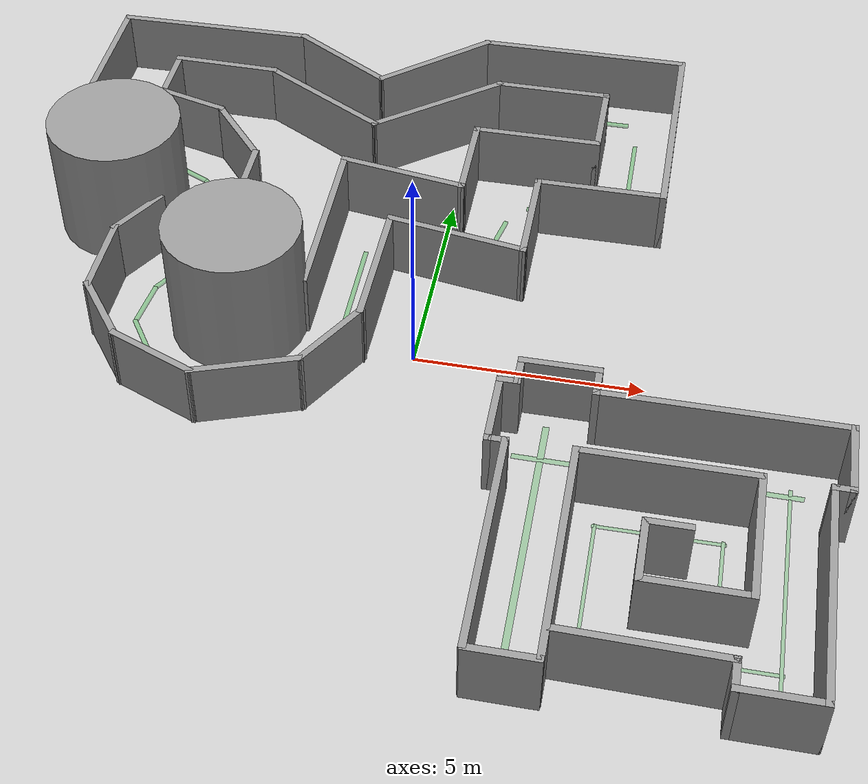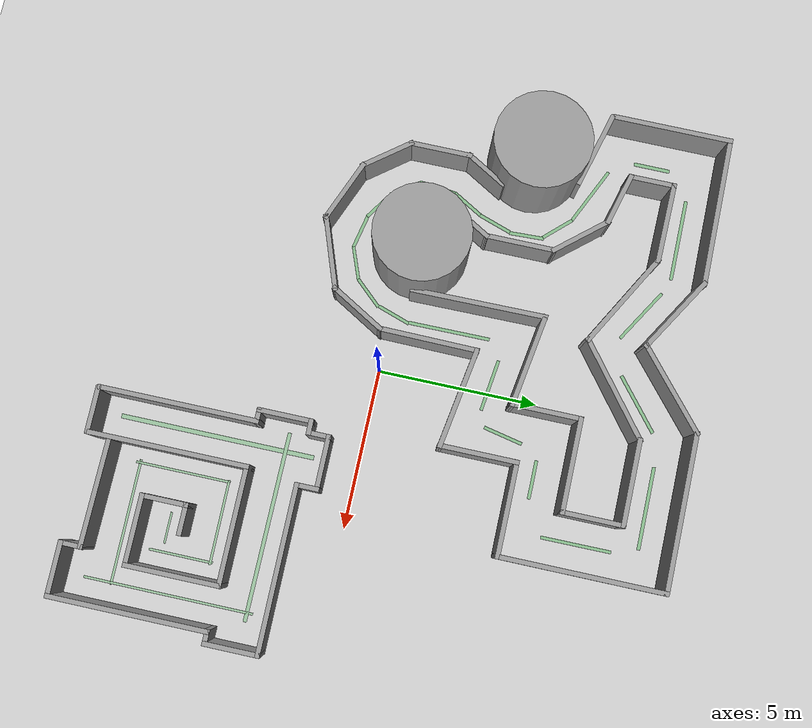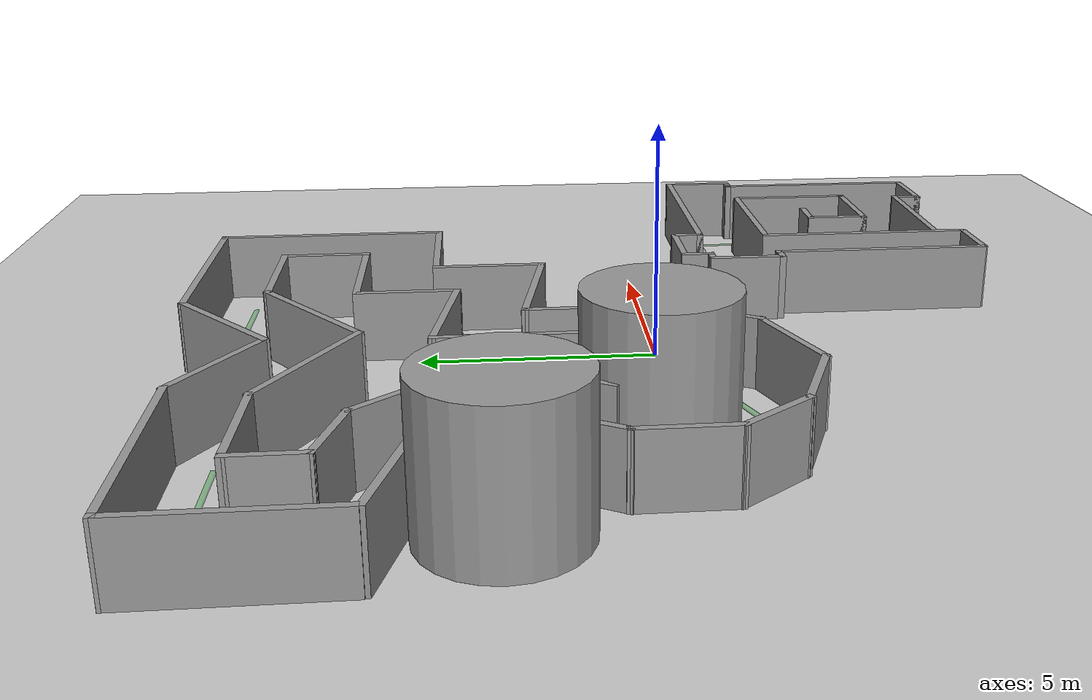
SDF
<sdf version="1.7">
 <world name="default">
  <light name="sun" type="directional">
   <pose>0 0 10 0 -0 0</pose>
   <diffuse>0.8 0.8 0.8 1</diffuse>
   <specular>0.2 0.2 0.2 1</specular>
   <attenuation>
    <range>1000</range>
    <constant>0.9</constant>
    <linear>0.01</linear>
    <quadratic>0.001</quadratic>
   </attenuation>
   <direction>-0.5 0.1 -0.9</direction>
   <spot><inner_angle>0</inner_angle><outer_angle>0</outer_angle><falloff>0</falloff></spot>
  </light>
  <model name="ground_plane">
   <static>1</static>
   <link name="link">
    <collision name="collision">
     <geometry><plane><normal>0 0 1</normal><size>100 100</size></plane></geometry>
     <surface>
      <contact><collide_bitmask>65535</collide_bitmask></contact>
      <friction><ode><mu>100</mu><mu2>50</mu2></ode></friction>
     </surface>
    </collision>
    <visual name="visual">
     <cast_shadows>0</cast_shadows>
     <geometry><plane><normal>0 0 1</normal><size>100 100</size></plane></geometry>
     <material>
      <script><uri>file://media/materials/scripts/gazebo.material</uri><name>Gazebo/Grey</name></script>
     </material>
    </visual>
   </link>
  </model>
  <gravity>0 0 -9.8</gravity>
  <magnetic_field>6e-06 2.3e-05 -4.2e-05</magnetic_field>
  <atmosphere type="adiabatic"/>
  <physics type="ode">
   <max_step_size>0.001</max_step_size>
   <real_time_factor>1</real_time_factor>
   <real_time_update_rate>1000</real_time_update_rate>
  </physics>
  <scene><ambient>0.4 0.4 0.4 1</ambient><background>0.7 0.7 0.7 1</background><shadows>1</shadows></scene>
  <spherical_coordinates>
   <surface_model>EARTH_WGS84</surface_model>
   <latitude_deg>0</latitude_deg>
   <longitude_deg>0</longitude_deg>
   <elevation>0</elevation>
   <heading_deg>0</heading_deg>
  </spherical_coordinates>
  <model name="map_1">
   <pose>5.62551 -4.52661 0 0 -0 0</pose>
   <link name="Wall_0">
    <collision name="Wall_0_Collision">
     <geometry><box><size>5 0.15 1.5</size></box></geometry>
     <pose>0 0 0.75 0 -0 0</pose>
    </collision>
    <visual name="Wall_0_Visual">
     <pose>0 0 0.75 0 -0 0</pose>
     <geometry><box><size>5 0.15 1.5</size></box></geometry>
     <material>
      <script><uri>file://media/materials/scripts/gazebo.material</uri><name>Gazebo/Grey</name></script>
      <ambient>1 1 1 1</ambient>
     </material>
     <meta><layer>0</layer></meta>
    </visual>
    <pose>-3.175 -1.10709 0 0 -0 1.5708</pose>
   </link>
   <link name="Wall_1">
    <collision name="Wall_1_Collision">
     <geometry><box><size>0.5 0.15 1.5</size></box></geometry>
     <pose>0 0 0.75 0 -0 0</pose>
    </collision>
    <visual name="Wall_1_Visual">
     <pose>0 0 0.75 0 -0 0</pose>
     <geometry><box><size>0.5 0.15 1.5</size></box></geometry>
     <material>
      <script><uri>file://media/materials/scripts/gazebo.material</uri><name>Gazebo/Grey</name></script>
      <ambient>1 1 1 1</ambient>
     </material>
     <meta><layer>0</layer></meta>
    </visual>
    <pose>-3.35 1.31791 0 0 -0 3.14159</pose>
   </link>
   <link name="Wall_10">
    <collision name="Wall_10_Collision">
     <geometry><box><size>5.25 0.15 1.5</size></box></geometry>
     <pose>0 0 0.75 0 -0 0</pose>
    </collision>
    <visual name="Wall_10_Visual">
     <pose>0 0 0.75 0 -0 0</pose>
     <geometry><box><size>5.25 0.15 1.5</size></box></geometry>
     <material>
      <script><uri>file://media/materials/scripts/gazebo.material</uri><name>Gazebo/Grey</name></script>
      <ambient>1 1 1 1</ambient>
     </material>
     <meta><layer>0</layer></meta>
    </visual>
    <pose>0.975 2.91791 0 0 -0 0</pose>
   </link>
   <link name="Wall_11">
    <collision name="Wall_11_Collision">
     <geometry><box><size>1.75 0.15 1.5</size></box></geometry>
     <pose>0 0 0.75 0 -0 0</pose>
    </collision>
    <visual name="Wall_11_Visual">
     <pose>0 0 0.75 0 -0 0</pose>
     <geometry><box><size>1.75 0.15 1.5</size></box></geometry>
     <material>
      <script><uri>file://media/materials/scripts/gazebo.material</uri><name>Gazebo/Grey</name></script>
      <ambient>1 1 1 1</ambient>
     </material>
     <meta><layer>0</layer></meta>
    </visual>
    <pose>3.525 2.11791 0 0 -0 -1.5708</pose>
   </link>
   <link name="Wall_12">
    <collision name="Wall_12_Collision">
     <geometry><box><size>0.5 0.15 1.5</size></box></geometry>
     <pose>0 0 0.75 0 -0 0</pose>
    </collision>
    <visual name="Wall_12_Visual">
     <pose>0 0 0.75 0 -0 0</pose>
     <geometry><box><size>0.5 0.15 1.5</size></box></geometry>
     <material>
      <script><uri>file://media/materials/scripts/gazebo.material</uri><name>Gazebo/Grey</name></script>
      <ambient>1 1 1 1</ambient>
     </material>
     <meta><layer>0</layer></meta>
    </visual>
    <pose>3.35 1.31791 0 0 -0 3.14159</pose>
   </link>
   <link name="Wall_13">
    <collision name="Wall_13_Collision">
     <geometry><box><size>5 0.15 1.5</size></box></geometry>
     <pose>0 0 0.75 0 -0 0</pose>
    </collision>
    <visual name="Wall_13_Visual">
     <pose>0 0 0.75 0 -0 0</pose>
     <geometry><box><size>5 0.15 1.5</size></box></geometry>
     <material>
      <script><uri>file://media/materials/scripts/gazebo.material</uri><name>Gazebo/Grey</name></script>
      <ambient>1 1 1 1</ambient>
     </material>
     <meta><layer>0</layer></meta>
    </visual>
    <pose>3.175 -1.10709 0 0 -0 -1.5708</pose>
   </link>
   <link name="Wall_14">
    <collision name="Wall_14_Collision">
     <geometry><box><size>1.75 0.15 1.5</size></box></geometry>
     <pose>0 0 0.75 0 -0 0</pose>
    </collision>
    <visual name="Wall_14_Visual">
     <pose>0 0 0.75 0 -0 0</pose>
     <geometry><box><size>1.75 0.15 1.5</size></box></geometry>
     <material>
      <script><uri>file://media/materials/scripts/gazebo.material</uri><name>Gazebo/Grey</name></script>
      <ambient>1 1 1 1</ambient>
     </material>
     <meta><layer>0</layer></meta>
    </visual>
    <pose>2.375 -3.53209 0 0 -0 3.14159</pose>
   </link>
   <link name="Wall_15">
    <collision name="Wall_15_Collision">
     <geometry><box><size>0.75 0.15 1.5</size></box></geometry>
     <pose>0 0 0.75 0 -0 0</pose>
    </collision>
    <visual name="Wall_15_Visual">
     <pose>0 0 0.75 0 -0 0</pose>
     <geometry><box><size>0.75 0.15 1.5</size></box></geometry>
     <material>
      <script><uri>file://media/materials/scripts/gazebo.material</uri><name>Gazebo/Grey</name></script>
      <ambient>1 1 1 1</ambient>
     </material>
     <meta><layer>0</layer></meta>
    </visual>
    <pose>1.575 -3.23209 0 0 -0 1.5708</pose>
   </link>
   <link name="Wall_18">
    <collision name="Wall_18_Collision">
     <geometry><box><size>5 0.15 1.5</size></box></geometry>
     <pose>0 0 0.75 0 -0 0</pose>
    </collision>
    <visual name="Wall_18_Visual">
     <pose>0 0 0.75 0 -0 0</pose>
     <geometry><box><size>5 0.15 1.5</size></box></geometry>
     <material>
      <script><uri>file://media/materials/scripts/gazebo.material</uri><name>Gazebo/Grey</name></script>
      <ambient>1 1 1 1</ambient>
     </material>
     <meta><layer>0</layer></meta>
    </visual>
    <pose>-1.787 -1.08609 0 0 -0 1.5708</pose>
   </link>
   <link name="Wall_19">
    <collision name="Wall_19_Collision">
     <geometry><box><size>3.75 0.15 1.5</size></box></geometry>
     <pose>0 0 0.75 0 -0 0</pose>
    </collision>
    <visual name="Wall_19_Visual">
     <pose>0 0 0.75 0 -0 0</pose>
     <geometry><box><size>3.75 0.15 1.5</size></box></geometry>
     <material>
      <script><uri>file://media/materials/scripts/gazebo.material</uri><name>Gazebo/Grey</name></script>
      <ambient>1 1 1 1</ambient>
     </material>
     <meta><layer>0</layer></meta>
    </visual>
    <pose>0.013 1.33891 0 0 -0 0</pose>
   </link>
   <link name="Wall_2">
    <collision name="Wall_2_Collision">
     <geometry><box><size>1.75 0.15 1.5</size></box></geometry>
     <pose>0 0 0.75 0 -0 0</pose>
    </collision>
    <visual name="Wall_2_Visual">
     <pose>0 0 0.75 0 -0 0</pose>
     <geometry><box><size>1.75 0.15 1.5</size></box></geometry>
     <material>
      <script><uri>file://media/materials/scripts/gazebo.material</uri><name>Gazebo/Grey</name></script>
      <ambient>1 1 1 1</ambient>
     </material>
     <meta><layer>0</layer></meta>
    </visual>
    <pose>-3.525 2.11791 0 0 -0 1.5708</pose>
   </link>
   <link name="Wall_20">
    <collision name="Wall_20_Collision">
     <geometry><box><size>3 0.15 1.5</size></box></geometry>
     <pose>0 0 0.75 0 -0 0</pose>
    </collision>
    <visual name="Wall_20_Visual">
     <pose>0 0 0.75 0 -0 0</pose>
     <geometry><box><size>3 0.15 1.5</size></box></geometry>
     <material>
      <script><uri>file://media/materials/scripts/gazebo.material</uri><name>Gazebo/Grey</name></script>
      <ambient>1 1 1 1</ambient>
     </material>
     <meta><layer>0</layer></meta>
    </visual>
    <pose>1.813 -0.086086 0 0 -0 -1.5708</pose>
   </link>
   <link name="Wall_21">
    <collision name="Wall_21_Collision">
     <geometry><box><size>2.25 0.15 1.5</size></box></geometry>
     <pose>0 0 0.75 0 -0 0</pose>
    </collision>
    <visual name="Wall_21_Visual">
     <pose>0 0 0.75 0 -0 0</pose>
     <geometry><box><size>2.25 0.15 1.5</size></box></geometry>
     <material>
      <script><uri>file://media/materials/scripts/gazebo.material</uri><name>Gazebo/Grey</name></script>
      <ambient>1 1 1 1</ambient>
     </material>
     <meta><layer>0</layer></meta>
    </visual>
    <pose>0.763 -1.51109 0 0 -0 3.14159</pose>
   </link>
   <link name="Wall_22">
    <collision name="Wall_22_Collision">
     <geometry><box><size>1.5 0.15 1.5</size></box></geometry>
     <pose>0 0 0.75 0 -0 0</pose>
    </collision>
    <visual name="Wall_22_Visual">
     <pose>0 0 0.75 0 -0 0</pose>
     <geometry><box><size>1.5 0.15 1.5</size></box></geometry>
     <material>
      <script><uri>file://media/materials/scripts/gazebo.material</uri><name>Gazebo/Grey</name></script>
      <ambient>1 1 1 1</ambient>
     </material>
     <meta><layer>0</layer></meta>
    </visual>
    <pose>-0.287 -0.836086 0 0 -0 1.5708</pose>
   </link>
   <link name="Wall_23">
    <collision name="Wall_23_Collision">
     <geometry><box><size>1 0.15 1.5</size></box></geometry>
     <pose>0 0 0.75 0 -0 0</pose>
    </collision>
    <visual name="Wall_23_Visual">
     <pose>0 0 0.75 0 -0 0</pose>
     <geometry><box><size>1 0.15 1.5</size></box></geometry>
     <material>
      <script><uri>file://media/materials/scripts/gazebo.material</uri><name>Gazebo/Grey</name></script>
      <ambient>1 1 1 1</ambient>
     </material>
     <meta><layer>0</layer></meta>
    </visual>
    <pose>0.138 -0.161086 0 0 -0 0</pose>
   </link>
   <link name="Wall_25">
    <collision name="Wall_25_Collision">
     <geometry><box><size>3.49004 0.15 1.5</size></box></geometry>
     <pose>0 0 0.75 0 -0 0</pose>
    </collision>
    <visual name="Wall_25_Visual">
     <pose>0 0 0.75 0 -0 0</pose>
     <geometry><box><size>3.49004 0.15 1.5</size></box></geometry>
     <material>
      <script><uri>file://media/materials/scripts/gazebo.material</uri><name>Gazebo/Grey</name></script>
      <ambient>1 1 1 1</ambient>
     </material>
     <meta><layer>0</layer></meta>
    </visual>
    <pose>-0.0945 -2.90709 0 0 -0 -0.014973</pose>
   </link>
   <link name="Wall_3">
    <collision name="Wall_3_Collision">
     <geometry><box><size>0.5 0.15 1.5</size></box></geometry>
     <pose>0 0 0.75 0 -0 0</pose>
    </collision>
    <visual name="Wall_3_Visual">
     <pose>0 0 0.75 0 -0 0</pose>
     <geometry><box><size>0.5 0.15 1.5</size></box></geometry>
     <material>
      <script><uri>file://media/materials/scripts/gazebo.material</uri><name>Gazebo/Grey</name></script>
      <ambient>1 1 1 1</ambient>
     </material>
     <meta><layer>0</layer></meta>
    </visual>
    <pose>-3.35 2.91791 0 0 -0 0</pose>
   </link>
   <link name="Wall_7">
    <collision name="Wall_7_Collision">
     <geometry><box><size>0.764 0.15 1.5</size></box></geometry>
     <pose>0 0 0.75 0 -0 0</pose>
    </collision>
    <visual name="Wall_7_Visual">
     <pose>0 0 0.75 0 -0 0</pose>
     <geometry><box><size>0.764 0.15 1.5</size></box></geometry>
     <material>
      <script><uri>file://media/materials/scripts/gazebo.material</uri><name>Gazebo/Grey</name></script>
      <ambient>1 1 1 1</ambient>
     </material>
     <meta><layer>0</layer></meta>
    </visual>
    <pose>-3.175 3.22492 0 0 -0 1.5708</pose>
   </link>
   <link name="Wall_8">
    <collision name="Wall_8_Collision">
     <geometry><box><size>1.75 0.15 1.5</size></box></geometry>
     <pose>0 0 0.75 0 -0 0</pose>
    </collision>
    <visual name="Wall_8_Visual">
     <pose>0 0 0.75 0 -0 0</pose>
     <geometry><box><size>1.75 0.15 1.5</size></box></geometry>
     <material>
      <script><uri>file://media/materials/scripts/gazebo.material</uri><name>Gazebo/Grey</name></script>
      <ambient>1 1 1 1</ambient>
     </material>
     <meta><layer>0</layer></meta>
    </visual>
    <pose>-2.375 3.53191 0 0 -0 0</pose>
   </link>
   <link name="Wall_9">
    <collision name="Wall_9_Collision">
     <geometry><box><size>0.764343 0.15 1.5</size></box></geometry>
     <pose>0 0 0.75 0 -0 0</pose>
    </collision>
    <visual name="Wall_9_Visual">
     <pose>0 0 0.75 0 -0 0</pose>
     <geometry><box><size>0.764343 0.15 1.5</size></box></geometry>
     <material>
      <script><uri>file://media/materials/scripts/gazebo.material</uri><name>Gazebo/Grey</name></script>
      <ambient>1 1 1 1</ambient>
     </material>
     <meta><layer>0</layer></meta>
    </visual>
    <pose>-1.575 3.22492 0 0 -0 -1.5708</pose>
   </link>
   <static>1</static>
  </model>
  <model name="wall_chiusura">
   <pose>4.04122 -6.40261 0 0 -0 0</pose>
   <link name="Wall_5">
    <collision name="Wall_5_Collision">
     <geometry><box><size>1.5 0.15 1.5</size></box></geometry>
     <pose>0 0 0.75 0 -0 0</pose>
    </collision>
    <visual name="Wall_5_Visual">
     <pose>0 0 0.75 0 -0 0</pose>
     <geometry><box><size>1.5 0.15 1.5</size></box></geometry>
     <material>
      <script><uri>file://media/materials/scripts/gazebo.material</uri><name>Gazebo/Grey</name></script>
      <ambient>1 1 1 1</ambient>
     </material>
     <meta><layer>0</layer></meta>
    </visual>
    <pose>-0.8875 -1.6975 0 0 -0 0</pose>
   </link>
   <static>1</static>
  </model>
  <model name="map_1_spawn">
   <link name="spawn_1">
    <inertial>
     <mass>0.0217086</mass>
     <inertia>
      <ixx>0.0556801</ixx>
      <ixy>0</ixy>
      <ixz>0</ixz>
      <iyy>7.146e-05</iyy>
      <iyz>0</iyz>
      <izz>0.0557501</izz>
     </inertia>
    </inertial>
    <pose>-2.6628 0.21384 0 0 -0 0</pose>
    <gravity>0</gravity>
    <visual name="visual">
     <geometry><box><size>0.13925 6.14907 0.019742</size></box></geometry>
     <material>
      <lighting>1</lighting>
      <script><uri>file://media/materials/scripts/gazebo.material</uri><name>Gazebo/Green</name></script>
      <shader type="pixel"><normal_map>__default__</normal_map></shader>
      <ambient>0 1 0 1</ambient>
      <diffuse>0 1 0 1</diffuse>
      <specular>0.1 0.1 0.1 1</specular>
      <emissive>0 0 0 1</emissive>
     </material>
     <transparency>0.7</transparency>
    </visual>
   </link>
   <link name="spawn_2">
    <inertial>
     <mass>0.0217086</mass>
     <inertia>
      <ixx>0.0556801</ixx>
      <ixy>0</ixy>
      <ixz>0</ixz>
      <iyy>7.146e-05</iyy>
      <iyz>0</iyz>
      <izz>0.0557501</izz>
     </inertia>
    </inertial>
    <pose>-0.293424 2.36477 0 0 0 -1.57852</pose>
    <gravity>0</gravity>
    <visual name="visual">
     <geometry><box><size>0.114656 5.93564 0.019742</size></box></geometry>
     <material>
      <lighting>1</lighting>
      <script><uri>file://media/materials/scripts/gazebo.material</uri><name>Gazebo/Green</name></script>
      <shader type="pixel"><normal_map>__default__</normal_map></shader>
      <ambient>0 1 0 1</ambient>
      <diffuse>0 1 0 1</diffuse>
      <specular>0.1 0.1 0.1 1</specular>
      <emissive>0 0 0 1</emissive>
     </material>
     <transparency>0.7</transparency>
    </visual>
   </link>
   <link name="spawn_3">
    <inertial>
     <mass>0.0217086</mass>
     <inertia>
      <ixx>0.0556801</ixx>
      <ixy>0</ixy>
      <ixz>0</ixz>
      <iyy>7.146e-05</iyy>
      <iyz>0</iyz>
      <izz>0.0557501</izz>
     </inertia>
    </inertial>
    <pose>2.39206 -0.132071 0 0 -0 0</pose>
    <gravity>0</gravity>
    <visual name="visual">
     <geometry><box><size>0.07165 5.33323 0.019742</size></box></geometry>
     <material>
      <lighting>1</lighting>
      <script><uri>file://media/materials/scripts/gazebo.material</uri><name>Gazebo/Green</name></script>
      <shader type="pixel"><normal_map>__default__</normal_map></shader>
      <ambient>0 1 0 1</ambient>
      <diffuse>0 1 0 1</diffuse>
      <specular>0.1 0.1 0.1 1</specular>
      <emissive>0 0 0 1</emissive>
     </material>
     <transparency>0.7</transparency>
    </visual>
   </link>
   <link name="spawn_4">
    <inertial>
     <mass>0.0217086</mass>
     <inertia>
      <ixx>0.0556801</ixx>
      <ixy>0</ixy>
      <ixz>0</ixz>
      <iyy>7.146e-05</iyy>
      <iyz>0</iyz>
      <izz>0.0557501</izz>
     </inertia>
    </inertial>
    <pose>0.493897 -1.93364 0 0 -0 1.57253</pose>
    <gravity>0</gravity>
    <visual name="visual">
     <geometry><box><size>0.07165 3.91941 0.019742</size></box></geometry>
     <material>
      <lighting>1</lighting>
      <script><uri>file://media/materials/scripts/gazebo.material</uri><name>Gazebo/Green</name></script>
      <shader type="pixel"><normal_map>__default__</normal_map></shader>
      <ambient>0 1 0 1</ambient>
      <diffuse>0 1 0 1</diffuse>
      <specular>0.1 0.1 0.1 1</specular>
      <emissive>0 0 0 1</emissive>
     </material>
     <transparency>0.7</transparency>
    </visual>
   </link>
   <link name="spawn_5">
    <inertial>
     <mass>0.0217086</mass>
     <inertia>
      <ixx>0.0556801</ixx>
      <ixy>0</ixy>
      <ixz>0</ixz>
      <iyy>7.146e-05</iyy>
      <iyz>0</iyz>
      <izz>0.0557501</izz>
     </inertia>
    </inertial>
    <pose>-1.37156 -0.565564 0 0 -0 0</pose>
    <gravity>0</gravity>
    <visual name="visual">
     <geometry><box><size>0.07165 3.00443 0.019742</size></box></geometry>
     <material>
      <lighting>1</lighting>
      <script><uri>file://media/materials/scripts/gazebo.material</uri><name>Gazebo/Green</name></script>
      <shader type="pixel"><normal_map>__default__</normal_map></shader>
      <ambient>0 1 0 1</ambient>
      <diffuse>0 1 0 1</diffuse>
      <specular>0.1 0.1 0.1 1</specular>
      <emissive>0 0 0 1</emissive>
     </material>
     <transparency>0.7</transparency>
    </visual>
   </link>
   <link name="spawn_6">
    <inertial>
     <mass>0.0217086</mass>
     <inertia>
      <ixx>0.0556801</ixx>
      <ixy>0</ixy>
      <ixz>0</ixz>
      <iyy>7.146e-05</iyy>
      <iyz>0</iyz>
      <izz>0.0557501</izz>
     </inertia>
    </inertial>
    <pose>1.15079 -0.034248 0 0 -0 0</pose>
    <gravity>0</gravity>
    <visual name="visual">
     <geometry><box><size>0.07165 2.01062 0.019742</size></box></geometry>
     <material>
      <lighting>1</lighting>
      <script><uri>file://media/materials/scripts/gazebo.material</uri><name>Gazebo/Green</name></script>
      <shader type="pixel"><normal_map>__default__</normal_map></shader>
      <ambient>0 1 0 1</ambient>
      <diffuse>0 1 0 1</diffuse>
      <specular>0.1 0.1 0.1 1</specular>
      <emissive>0 0 0 1</emissive>
     </material>
     <transparency>0.7</transparency>
    </visual>
   </link>
   <link name="spawn_7">
    <inertial>
     <mass>0.0217086</mass>
     <inertia>
      <ixx>0.0556801</ixx>
      <ixy>0</ixy>
      <ixz>0</ixz>
      <iyy>7.146e-05</iyy>
      <iyz>0</iyz>
      <izz>0.0557501</izz>
     </inertia>
    </inertial>
    <pose>0.397758 -0.623377 0 0 -0 1.56719</pose>
    <gravity>0</gravity>
    <visual name="visual">
     <geometry><box><size>0.05862 0.979625 0.019742</size></box></geometry>
     <material>
      <lighting>1</lighting>
      <script><uri>file://media/materials/scripts/gazebo.material</uri><name>Gazebo/Green</name></script>
      <shader type="pixel"><normal_map>__default__</normal_map></shader>
      <ambient>0 1 0 1</ambient>
      <diffuse>0 1 0 1</diffuse>
      <specular>0.1 0.1 0.1 1</specular>
      <emissive>0 0 0 1</emissive>
     </material>
     <transparency>0.7</transparency>
    </visual>
   </link>
   <link name="spawn_8">
    <inertial>
     <mass>0.0217086</mass>
     <inertia>
      <ixx>0.0556801</ixx>
      <ixy>0</ixy>
      <ixz>0</ixz>
      <iyy>7.146e-05</iyy>
      <iyz>0</iyz>
      <izz>0.0557501</izz>
     </inertia>
    </inertial>
    <pose>-0.106085 0.888692 0 0 -0 1.57519</pose>
    <gravity>0</gravity>
    <visual name="visual">
     <geometry><box><size>0.07165 2.65164 0.019742</size></box></geometry>
     <material>
      <lighting>1</lighting>
      <script><uri>file://media/materials/scripts/gazebo.material</uri><name>Gazebo/Green</name></script>
      <shader type="pixel"><normal_map>__default__</normal_map></shader>
      <ambient>0 1 0 1</ambient>
      <diffuse>0 1 0 1</diffuse>
      <specular>0.1 0.1 0.1 1</specular>
      <emissive>0 0 0 1</emissive>
     </material>
     <transparency>0.7</transparency>
    </visual>
   </link>
   <static>1</static>
   <pose>5.74909 -4.69174 0 0 -0 0</pose>
  </model>
  <model name="map_2">
   <link name="Wall_10">
    <pose>4.01324 4.53292 0 0 -0 3.14159</pose>
    <visual name="Wall_10_Visual">
     <pose>0 0 0.75 0 -0 0</pose>
     <geometry><box><size>2.75 0.15 1.5</size></box></geometry>
     <material>
      <script><uri>file://media/materials/scripts/gazebo.material</uri><name>Gazebo/Grey</name></script>
      <ambient>1 1 1 1</ambient>
      <shader type="pixel"/>
     </material>
     <meta><layer>0</layer></meta>
    </visual>
    <collision name="Wall_10_Collision">
     <pose>0 0 0.75 0 -0 0</pose>
     <geometry><box><size>2.75 0.15 1.5</size></box></geometry>
     <surface>
      <friction>
       <ode><mu>1</mu><mu2>1</mu2><fdir1>0 0 0</fdir1><slip1>0</slip1><slip2>0</slip2></ode>
       <torsional>
        <coefficient>1</coefficient>
        <patch_radius>0</patch_radius>
        <surface_radius>0</surface_radius>
        <use_patch_radius>1</use_patch_radius>
        <ode><slip>0</slip></ode>
       </torsional>
      </friction>
      <bounce><restitution_coefficient>0</restitution_coefficient><threshold>1e+06</threshold></bounce>
      <contact>
       <collide_without_contact>0</collide_without_contact>
       <collide_without_contact_bitmask>1</collide_without_contact_bitmask>
       <collide_bitmask>1</collide_bitmask>
       <ode>
        <soft_cfm>0</soft_cfm>
        <soft_erp>0.2</soft_erp>
        <kp>1e+13</kp>
        <kd>1</kd>
        <max_vel>0.01</max_vel>
        <min_depth>0</min_depth>
       </ode>
       <bullet>
        <split_impulse>1</split_impulse>
        <split_impulse_penetration_threshold>-0.01</split_impulse_penetration_threshold>
        <soft_cfm>0</soft_cfm>
        <soft_erp>0.2</soft_erp>
        <kp>1e+13</kp>
        <kd>1</kd>
       </bullet>
      </contact>
     </surface>
    </collision>
   </link>
   <link name="Wall_12">
    <pose>1.38174 3.48292 0 0 -0 0.667741</pose>
    <visual name="Wall_12_Visual">
     <pose>0 0 0.75 0 -0 0</pose>
     <geometry><box><size>3.54164 0.15 1.5</size></box></geometry>
     <material>
      <script><uri>file://media/materials/scripts/gazebo.material</uri><name>Gazebo/Grey</name></script>
      <ambient>1 1 1 1</ambient>
      <shader type="pixel"/>
     </material>
     <meta><layer>0</layer></meta>
    </visual>
    <collision name="Wall_12_Collision">
     <pose>0 0 0.75 0 -0 0</pose>
     <geometry><box><size>3.54164 0.15 1.5</size></box></geometry>
     <surface>
      <friction>
       <ode><mu>1</mu><mu2>1</mu2><fdir1>0 0 0</fdir1><slip1>0</slip1><slip2>0</slip2></ode>
       <torsional>
        <coefficient>1</coefficient>
        <patch_radius>0</patch_radius>
        <surface_radius>0</surface_radius>
        <use_patch_radius>1</use_patch_radius>
        <ode><slip>0</slip></ode>
       </torsional>
      </friction>
      <bounce><restitution_coefficient>0</restitution_coefficient><threshold>1e+06</threshold></bounce>
      <contact>
       <collide_without_contact>0</collide_without_contact>
       <collide_without_contact_bitmask>1</collide_without_contact_bitmask>
       <collide_bitmask>1</collide_bitmask>
       <ode>
        <soft_cfm>0</soft_cfm>
        <soft_erp>0.2</soft_erp>
        <kp>1e+13</kp>
        <kd>1</kd>
        <max_vel>0.01</max_vel>
        <min_depth>0</min_depth>
       </ode>
       <bullet>
        <split_impulse>1</split_impulse>
        <split_impulse_penetration_threshold>-0.01</split_impulse_penetration_threshold>
        <soft_cfm>0</soft_cfm>
        <soft_erp>0.2</soft_erp>
        <kp>1e+13</kp>
        <kd>1</kd>
       </bullet>
      </contact>
     </surface>
    </collision>
   </link>
   <link name="Wall_14">
    <pose>-1.37776 3.23742 0 0 0 -0.513054</pose>
    <visual name="Wall_14_Visual">
     <pose>0 0 0.75 0 -0 0</pose>
     <geometry><box><size>3.42797 0.15 1.5</size></box></geometry>
     <material>
      <script><uri>file://media/materials/scripts/gazebo.material</uri><name>Gazebo/Grey</name></script>
      <ambient>1 1 1 1</ambient>
      <shader type="pixel"/>
     </material>
     <meta><layer>0</layer></meta>
    </visual>
    <collision name="Wall_14_Collision">
     <pose>0 0 0.75 0 -0 0</pose>
     <geometry><box><size>3.42797 0.15 1.5</size></box></geometry>
     <surface>
      <friction>
       <ode><mu>1</mu><mu2>1</mu2><fdir1>0 0 0</fdir1><slip1>0</slip1><slip2>0</slip2></ode>
       <torsional>
        <coefficient>1</coefficient>
        <patch_radius>0</patch_radius>
        <surface_radius>0</surface_radius>
        <use_patch_radius>1</use_patch_radius>
        <ode><slip>0</slip></ode>
       </torsional>
      </friction>
      <bounce><restitution_coefficient>0</restitution_coefficient><threshold>1e+06</threshold></bounce>
      <contact>
       <collide_without_contact>0</collide_without_contact>
       <collide_without_contact_bitmask>1</collide_without_contact_bitmask>
       <collide_bitmask>1</collide_bitmask>
       <ode>
        <soft_cfm>0</soft_cfm>
        <soft_erp>0.2</soft_erp>
        <kp>1e+13</kp>
        <kd>1</kd>
        <max_vel>0.01</max_vel>
        <min_depth>0</min_depth>
       </ode>
       <bullet>
        <split_impulse>1</split_impulse>
        <split_impulse_penetration_threshold>-0.01</split_impulse_penetration_threshold>
        <soft_cfm>0</soft_cfm>
        <soft_erp>0.2</soft_erp>
        <kp>1e+13</kp>
        <kd>1</kd>
       </bullet>
      </contact>
     </surface>
    </collision>
   </link>
   <link name="Wall_16">
    <pose>-4.01276 4.06192 0 0 0 -0.016568</pose>
    <visual name="Wall_16_Visual">
     <pose>0 0 0.75 0 -0 0</pose>
     <geometry><box><size>2.56379 0.15 1.5</size></box></geometry>
     <material>
      <script><uri>file://media/materials/scripts/gazebo.material</uri><name>Gazebo/Grey</name></script>
      <ambient>1 1 1 1</ambient>
      <shader type="pixel"/>
     </material>
     <meta><layer>0</layer></meta>
    </visual>
    <collision name="Wall_16_Collision">
     <pose>0 0 0.75 0 -0 0</pose>
     <geometry><box><size>2.56379 0.15 1.5</size></box></geometry>
     <surface>
      <friction>
       <ode><mu>1</mu><mu2>1</mu2><fdir1>0 0 0</fdir1><slip1>0</slip1><slip2>0</slip2></ode>
       <torsional>
        <coefficient>1</coefficient>
        <patch_radius>0</patch_radius>
        <surface_radius>0</surface_radius>
        <use_patch_radius>1</use_patch_radius>
        <ode><slip>0</slip></ode>
       </torsional>
      </friction>
      <bounce><restitution_coefficient>0</restitution_coefficient><threshold>1e+06</threshold></bounce>
      <contact>
       <collide_without_contact>0</collide_without_contact>
       <collide_without_contact_bitmask>1</collide_without_contact_bitmask>
       <collide_bitmask>1</collide_bitmask>
       <ode>
        <soft_cfm>0</soft_cfm>
        <soft_erp>0.2</soft_erp>
        <kp>1e+13</kp>
        <kd>1</kd>
        <max_vel>0.01</max_vel>
        <min_depth>0</min_depth>
       </ode>
       <bullet>
        <split_impulse>1</split_impulse>
        <split_impulse_penetration_threshold>-0.01</split_impulse_penetration_threshold>
        <soft_cfm>0</soft_cfm>
        <soft_erp>0.2</soft_erp>
        <kp>1e+13</kp>
        <kd>1</kd>
       </bullet>
      </contact>
     </surface>
    </collision>
   </link>
   <link name="Wall_18">
    <pose>-5.21976 3.40692 0 0 0 -1.5708</pose>
    <visual name="Wall_18_Visual">
     <pose>0 0 0.75 0 -0 0</pose>
     <geometry><box><size>1.5 0.15 1.5</size></box></geometry>
     <material>
      <script><uri>file://media/materials/scripts/gazebo.material</uri><name>Gazebo/Grey</name></script>
      <ambient>1 1 1 1</ambient>
      <shader type="pixel"/>
     </material>
     <meta><layer>0</layer></meta>
    </visual>
    <collision name="Wall_18_Collision">
     <pose>0 0 0.75 0 -0 0</pose>
     <geometry><box><size>1.5 0.15 1.5</size></box></geometry>
     <surface>
      <friction>
       <ode><mu>1</mu><mu2>1</mu2><fdir1>0 0 0</fdir1><slip1>0</slip1><slip2>0</slip2></ode>
       <torsional>
        <coefficient>1</coefficient>
        <patch_radius>0</patch_radius>
        <surface_radius>0</surface_radius>
        <use_patch_radius>1</use_patch_radius>
        <ode><slip>0</slip></ode>
       </torsional>
      </friction>
      <bounce><restitution_coefficient>0</restitution_coefficient><threshold>1e+06</threshold></bounce>
      <contact>
       <collide_without_contact>0</collide_without_contact>
       <collide_without_contact_bitmask>1</collide_without_contact_bitmask>
       <collide_bitmask>1</collide_bitmask>
       <ode>
        <soft_cfm>0</soft_cfm>
        <soft_erp>0.2</soft_erp>
        <kp>1e+13</kp>
        <kd>1</kd>
        <max_vel>0.01</max_vel>
        <min_depth>0</min_depth>
       </ode>
       <bullet>
        <split_impulse>1</split_impulse>
        <split_impulse_penetration_threshold>-0.01</split_impulse_penetration_threshold>
        <soft_cfm>0</soft_cfm>
        <soft_erp>0.2</soft_erp>
        <kp>1e+13</kp>
        <kd>1</kd>
       </bullet>
      </contact>
     </surface>
    </collision>
   </link>
   <link name="Wall_19">
    <pose>-4.44676 2.52492 0 0 0 -0.261649</pose>
    <visual name="Wall_19_Visual">
     <pose>0 0 0.75 0 -0 0</pose>
     <geometry><box><size>1.75 0.15 1.5</size></box></geometry>
     <material>
      <script><uri>file://media/materials/scripts/gazebo.material</uri><name>Gazebo/Grey</name></script>
      <ambient>1 1 1 1</ambient>
      <shader type="pixel"/>
     </material>
     <meta><layer>0</layer></meta>
    </visual>
    <collision name="Wall_19_Collision">
     <pose>0 0 0.75 0 -0 0</pose>
     <geometry><box><size>1.75 0.15 1.5</size></box></geometry>
     <surface>
      <friction>
       <ode><mu>1</mu><mu2>1</mu2><fdir1>0 0 0</fdir1><slip1>0</slip1><slip2>0</slip2></ode>
       <torsional>
        <coefficient>1</coefficient>
        <patch_radius>0</patch_radius>
        <surface_radius>0</surface_radius>
        <use_patch_radius>1</use_patch_radius>
        <ode><slip>0</slip></ode>
       </torsional>
      </friction>
      <bounce><restitution_coefficient>0</restitution_coefficient><threshold>1e+06</threshold></bounce>
      <contact>
       <collide_without_contact>0</collide_without_contact>
       <collide_without_contact_bitmask>1</collide_without_contact_bitmask>
       <collide_bitmask>1</collide_bitmask>
       <ode>
        <soft_cfm>0</soft_cfm>
        <soft_erp>0.2</soft_erp>
        <kp>1e+13</kp>
        <kd>1</kd>
        <max_vel>0.01</max_vel>
        <min_depth>0</min_depth>
       </ode>
       <bullet>
        <split_impulse>1</split_impulse>
        <split_impulse_penetration_threshold>-0.01</split_impulse_penetration_threshold>
        <soft_cfm>0</soft_cfm>
        <soft_erp>0.2</soft_erp>
        <kp>1e+13</kp>
        <kd>1</kd>
       </bullet>
      </contact>
     </surface>
    </collision>
   </link>
   <link name="Wall_2">
    <pose>-0.335262 -1.03908 0 0 -0 1.5788</pose>
    <visual name="Wall_2_Visual">
     <pose>0 0 0.75 0 -0 0</pose>
     <geometry><box><size>4.27213 0.15 1.5</size></box></geometry>
     <material>
      <script><uri>file://media/materials/scripts/gazebo.material</uri><name>Gazebo/Grey</name></script>
      <ambient>1 1 1 1</ambient>
      <shader type="pixel"/>
     </material>
     <meta><layer>0</layer></meta>
    </visual>
    <collision name="Wall_2_Collision">
     <pose>0 0 0.75 0 -0 0</pose>
     <geometry><box><size>4.27213 0.15 1.5</size></box></geometry>
     <surface>
      <friction>
       <ode><mu>1</mu><mu2>1</mu2><fdir1>0 0 0</fdir1><slip1>0</slip1><slip2>0</slip2></ode>
       <torsional>
        <coefficient>1</coefficient>
        <patch_radius>0</patch_radius>
        <surface_radius>0</surface_radius>
        <use_patch_radius>1</use_patch_radius>
        <ode><slip>0</slip></ode>
       </torsional>
      </friction>
      <bounce><restitution_coefficient>0</restitution_coefficient><threshold>1e+06</threshold></bounce>
      <contact>
       <collide_without_contact>0</collide_without_contact>
       <collide_without_contact_bitmask>1</collide_without_contact_bitmask>
       <collide_bitmask>1</collide_bitmask>
       <ode>
        <soft_cfm>0</soft_cfm>
        <soft_erp>0.2</soft_erp>
        <kp>1e+13</kp>
        <kd>1</kd>
        <max_vel>0.01</max_vel>
        <min_depth>0</min_depth>
       </ode>
       <bullet>
        <split_impulse>1</split_impulse>
        <split_impulse_penetration_threshold>-0.01</split_impulse_penetration_threshold>
        <soft_cfm>0</soft_cfm>
        <soft_erp>0.2</soft_erp>
        <kp>1e+13</kp>
        <kd>1</kd>
       </bullet>
      </contact>
     </surface>
    </collision>
   </link>
   <link name="Wall_21">
    <pose>-3.05876 1.59092 0 0 -0 2.27293</pose>
    <visual name="Wall_21_Visual">
     <pose>0 0 0.75 0 -0 0</pose>
     <geometry><box><size>2.05434 0.15 1.5</size></box></geometry>
     <material>
      <script><uri>file://media/materials/scripts/gazebo.material</uri><name>Gazebo/Grey</name></script>
      <ambient>1 1 1 1</ambient>
      <shader type="pixel"/>
     </material>
     <meta><layer>0</layer></meta>
    </visual>
    <collision name="Wall_21_Collision">
     <pose>0 0 0.75 0 -0 0</pose>
     <geometry><box><size>2.05434 0.15 1.5</size></box></geometry>
     <surface>
      <friction>
       <ode><mu>1</mu><mu2>1</mu2><fdir1>0 0 0</fdir1><slip1>0</slip1><slip2>0</slip2></ode>
       <torsional>
        <coefficient>1</coefficient>
        <patch_radius>0</patch_radius>
        <surface_radius>0</surface_radius>
        <use_patch_radius>1</use_patch_radius>
        <ode><slip>0</slip></ode>
       </torsional>
      </friction>
      <bounce><restitution_coefficient>0</restitution_coefficient><threshold>1e+06</threshold></bounce>
      <contact>
       <collide_without_contact>0</collide_without_contact>
       <collide_without_contact_bitmask>1</collide_without_contact_bitmask>
       <collide_bitmask>1</collide_bitmask>
       <ode>
        <soft_cfm>0</soft_cfm>
        <soft_erp>0.2</soft_erp>
        <kp>1e+13</kp>
        <kd>1</kd>
        <max_vel>0.01</max_vel>
        <min_depth>0</min_depth>
       </ode>
       <bullet>
        <split_impulse>1</split_impulse>
        <split_impulse_penetration_threshold>-0.01</split_impulse_penetration_threshold>
        <soft_cfm>0</soft_cfm>
        <soft_erp>0.2</soft_erp>
        <kp>1e+13</kp>
        <kd>1</kd>
       </bullet>
      </contact>
     </surface>
    </collision>
   </link>
   <link name="Wall_42">
    <pose>-2.44376 -0.186078 0 0 0 -1.5708</pose>
    <visual name="Wall_42_Visual">
     <pose>0 0 0.75 0 -0 0</pose>
     <geometry><box><size>2.25 0.15 1.5</size></box></geometry>
     <material>
      <script><uri>file://media/materials/scripts/gazebo.material</uri><name>Gazebo/Grey</name></script>
      <ambient>1 1 1 1</ambient>
      <shader type="pixel"/>
     </material>
     <meta><layer>0</layer></meta>
    </visual>
    <collision name="Wall_42_Collision">
     <pose>0 0 0.75 0 -0 0</pose>
     <geometry><box><size>2.25 0.15 1.5</size></box></geometry>
     <surface>
      <friction>
       <ode><mu>1</mu><mu2>1</mu2><fdir1>0 0 0</fdir1><slip1>0</slip1><slip2>0</slip2></ode>
       <torsional>
        <coefficient>1</coefficient>
        <patch_radius>0</patch_radius>
        <surface_radius>0</surface_radius>
        <use_patch_radius>1</use_patch_radius>
        <ode><slip>0</slip></ode>
       </torsional>
      </friction>
      <bounce><restitution_coefficient>0</restitution_coefficient><threshold>1e+06</threshold></bounce>
      <contact>
       <collide_without_contact>0</collide_without_contact>
       <collide_without_contact_bitmask>1</collide_without_contact_bitmask>
       <collide_bitmask>1</collide_bitmask>
       <ode>
        <soft_cfm>0</soft_cfm>
        <soft_erp>0.2</soft_erp>
        <kp>1e+13</kp>
        <kd>1</kd>
        <max_vel>0.01</max_vel>
        <min_depth>0</min_depth>
       </ode>
       <bullet>
        <split_impulse>1</split_impulse>
        <split_impulse_penetration_threshold>-0.01</split_impulse_penetration_threshold>
        <soft_cfm>0</soft_cfm>
        <soft_erp>0.2</soft_erp>
        <kp>1e+13</kp>
        <kd>1</kd>
       </bullet>
      </contact>
     </surface>
    </collision>
   </link>
   <link name="Wall_43">
    <pose>-2.71876 -1.71208 0 0 0 -2.09468</pose>
    <visual name="Wall_43_Visual">
     <pose>0 0 0.75 0 -0 0</pose>
     <geometry><box><size>1.25 0.15 1.5</size></box></geometry>
     <material>
      <script><uri>file://media/materials/scripts/gazebo.material</uri><name>Gazebo/Grey</name></script>
      <ambient>1 1 1 1</ambient>
      <shader type="pixel"/>
     </material>
     <meta><layer>0</layer></meta>
    </visual>
    <collision name="Wall_43_Collision">
     <pose>0 0 0.75 0 -0 0</pose>
     <geometry><box><size>1.25 0.15 1.5</size></box></geometry>
     <surface>
      <friction>
       <ode><mu>1</mu><mu2>1</mu2><fdir1>0 0 0</fdir1><slip1>0</slip1><slip2>0</slip2></ode>
       <torsional>
        <coefficient>1</coefficient>
        <patch_radius>0</patch_radius>
        <surface_radius>0</surface_radius>
        <use_patch_radius>1</use_patch_radius>
        <ode><slip>0</slip></ode>
       </torsional>
      </friction>
      <bounce><restitution_coefficient>0</restitution_coefficient><threshold>1e+06</threshold></bounce>
      <contact>
       <collide_without_contact>0</collide_without_contact>
       <collide_without_contact_bitmask>1</collide_without_contact_bitmask>
       <collide_bitmask>1</collide_bitmask>
       <ode>
        <soft_cfm>0</soft_cfm>
        <soft_erp>0.2</soft_erp>
        <kp>1e+13</kp>
        <kd>1</kd>
        <max_vel>0.01</max_vel>
        <min_depth>0</min_depth>
       </ode>
       <bullet>
        <split_impulse>1</split_impulse>
        <split_impulse_penetration_threshold>-0.01</split_impulse_penetration_threshold>
        <soft_cfm>0</soft_cfm>
        <soft_erp>0.2</soft_erp>
        <kp>1e+13</kp>
        <kd>1</kd>
       </bullet>
      </contact>
     </surface>
    </collision>
   </link>
   <link name="Wall_45">
    <pose>-4.48526 -1.67358 0 0 0 -2.09444</pose>
    <visual name="Wall_45_Visual">
     <pose>0 0 0.75 0 -0 0</pose>
     <geometry><box><size>1.5 0.15 1.5</size></box></geometry>
     <material>
      <script><uri>file://media/materials/scripts/gazebo.material</uri><name>Gazebo/Grey</name></script>
      <ambient>1 1 1 1</ambient>
      <shader type="pixel"/>
     </material>
     <meta><layer>0</layer></meta>
    </visual>
    <collision name="Wall_45_Collision">
     <pose>0 0 0.75 0 -0 0</pose>
     <geometry><box><size>1.5 0.15 1.5</size></box></geometry>
     <surface>
      <friction>
       <ode><mu>1</mu><mu2>1</mu2><fdir1>0 0 0</fdir1><slip1>0</slip1><slip2>0</slip2></ode>
       <torsional>
        <coefficient>1</coefficient>
        <patch_radius>0</patch_radius>
        <surface_radius>0</surface_radius>
        <use_patch_radius>1</use_patch_radius>
        <ode><slip>0</slip></ode>
       </torsional>
      </friction>
      <bounce><restitution_coefficient>0</restitution_coefficient><threshold>1e+06</threshold></bounce>
      <contact>
       <collide_without_contact>0</collide_without_contact>
       <collide_without_contact_bitmask>1</collide_without_contact_bitmask>
       <collide_bitmask>1</collide_bitmask>
       <ode>
        <soft_cfm>0</soft_cfm>
        <soft_erp>0.2</soft_erp>
        <kp>1e+13</kp>
        <kd>1</kd>
        <max_vel>0.01</max_vel>
        <min_depth>0</min_depth>
       </ode>
       <bullet>
        <split_impulse>1</split_impulse>
        <split_impulse_penetration_threshold>-0.01</split_impulse_penetration_threshold>
        <soft_cfm>0</soft_cfm>
        <soft_erp>0.2</soft_erp>
        <kp>1e+13</kp>
        <kd>1</kd>
       </bullet>
      </contact>
     </surface>
    </collision>
   </link>
   <link name="Wall_46">
    <pose>-4.82276 -3.18308 0 0 0 -1.5708</pose>
    <visual name="Wall_46_Visual">
     <pose>0 0 0.75 0 -0 0</pose>
     <geometry><box><size>2 0.15 1.5</size></box></geometry>
     <material>
      <script><uri>file://media/materials/scripts/gazebo.material</uri><name>Gazebo/Grey</name></script>
      <ambient>1 1 1 1</ambient>
      <shader type="pixel"/>
     </material>
     <meta><layer>0</layer></meta>
    </visual>
    <collision name="Wall_46_Collision">
     <pose>0 0 0.75 0 -0 0</pose>
     <geometry><box><size>2 0.15 1.5</size></box></geometry>
     <surface>
      <friction>
       <ode><mu>1</mu><mu2>1</mu2><fdir1>0 0 0</fdir1><slip1>0</slip1><slip2>0</slip2></ode>
       <torsional>
        <coefficient>1</coefficient>
        <patch_radius>0</patch_radius>
        <surface_radius>0</surface_radius>
        <use_patch_radius>1</use_patch_radius>
        <ode><slip>0</slip></ode>
       </torsional>
      </friction>
      <bounce><restitution_coefficient>0</restitution_coefficient><threshold>1e+06</threshold></bounce>
      <contact>
       <collide_without_contact>0</collide_without_contact>
       <collide_without_contact_bitmask>1</collide_without_contact_bitmask>
       <collide_bitmask>1</collide_bitmask>
       <ode>
        <soft_cfm>0</soft_cfm>
        <soft_erp>0.2</soft_erp>
        <kp>1e+13</kp>
        <kd>1</kd>
        <max_vel>0.01</max_vel>
        <min_depth>0</min_depth>
       </ode>
       <bullet>
        <split_impulse>1</split_impulse>
        <split_impulse_penetration_threshold>-0.01</split_impulse_penetration_threshold>
        <soft_cfm>0</soft_cfm>
        <soft_erp>0.2</soft_erp>
        <kp>1e+13</kp>
        <kd>1</kd>
       </bullet>
      </contact>
     </surface>
    </collision>
   </link>
   <link name="Wall_48">
    <pose>-4.32126 -4.76258 0 0 -0 2.22461</pose>
    <visual name="Wall_48_Visual">
     <pose>0 0 0.75 0 -0 0</pose>
     <geometry><box><size>1.79931 0.15 1.5</size></box></geometry>
     <material>
      <script><uri>file://media/materials/scripts/gazebo.material</uri><name>Gazebo/Grey</name></script>
      <ambient>1 1 1 1</ambient>
      <shader type="pixel"/>
     </material>
     <meta><layer>0</layer></meta>
    </visual>
    <collision name="Wall_48_Collision">
     <pose>0 0 0.75 0 -0 0</pose>
     <geometry><box><size>1.79931 0.15 1.5</size></box></geometry>
     <surface>
      <friction>
       <ode><mu>1</mu><mu2>1</mu2><fdir1>0 0 0</fdir1><slip1>0</slip1><slip2>0</slip2></ode>
       <torsional>
        <coefficient>1</coefficient>
        <patch_radius>0</patch_radius>
        <surface_radius>0</surface_radius>
        <use_patch_radius>1</use_patch_radius>
        <ode><slip>0</slip></ode>
       </torsional>
      </friction>
      <bounce><restitution_coefficient>0</restitution_coefficient><threshold>1e+06</threshold></bounce>
      <contact>
       <collide_without_contact>0</collide_without_contact>
       <collide_without_contact_bitmask>1</collide_without_contact_bitmask>
       <collide_bitmask>1</collide_bitmask>
       <ode>
        <soft_cfm>0</soft_cfm>
        <soft_erp>0.2</soft_erp>
        <kp>1e+13</kp>
        <kd>1</kd>
        <max_vel>0.01</max_vel>
        <min_depth>0</min_depth>
       </ode>
       <bullet>
        <split_impulse>1</split_impulse>
        <split_impulse_penetration_threshold>-0.01</split_impulse_penetration_threshold>
        <soft_cfm>0</soft_cfm>
        <soft_erp>0.2</soft_erp>
        <kp>1e+13</kp>
        <kd>1</kd>
       </bullet>
      </contact>
     </surface>
    </collision>
   </link>
   <link name="Wall_5">
    <pose>1.05574 0.802422 0 0 -0 2.98689</pose>
    <visual name="Wall_5_Visual">
     <pose>0 0 0.75 0 -0 0</pose>
     <geometry><box><size>2.99933 0.15 1.5</size></box></geometry>
     <material>
      <script><uri>file://media/materials/scripts/gazebo.material</uri><name>Gazebo/Grey</name></script>
      <ambient>1 1 1 1</ambient>
      <shader type="pixel"/>
     </material>
     <meta><layer>0</layer></meta>
    </visual>
    <collision name="Wall_5_Collision">
     <pose>0 0 0.75 0 -0 0</pose>
     <geometry><box><size>2.99933 0.15 1.5</size></box></geometry>
     <surface>
      <friction>
       <ode><mu>1</mu><mu2>1</mu2><fdir1>0 0 0</fdir1><slip1>0</slip1><slip2>0</slip2></ode>
       <torsional>
        <coefficient>1</coefficient>
        <patch_radius>0</patch_radius>
        <surface_radius>0</surface_radius>
        <use_patch_radius>1</use_patch_radius>
        <ode><slip>0</slip></ode>
       </torsional>
      </friction>
      <bounce><restitution_coefficient>0</restitution_coefficient><threshold>1e+06</threshold></bounce>
      <contact>
       <collide_without_contact>0</collide_without_contact>
       <collide_without_contact_bitmask>1</collide_without_contact_bitmask>
       <collide_bitmask>1</collide_bitmask>
       <ode>
        <soft_cfm>0</soft_cfm>
        <soft_erp>0.2</soft_erp>
        <kp>1e+13</kp>
        <kd>1</kd>
        <max_vel>0.01</max_vel>
        <min_depth>0</min_depth>
       </ode>
       <bullet>
        <split_impulse>1</split_impulse>
        <split_impulse_penetration_threshold>-0.01</split_impulse_penetration_threshold>
        <soft_cfm>0</soft_cfm>
        <soft_erp>0.2</soft_erp>
        <kp>1e+13</kp>
        <kd>1</kd>
       </bullet>
      </contact>
     </surface>
    </collision>
   </link>
   <link name="Wall_51">
    <pose>-2.90126 -5.79458 0 0 -0 2.75164</pose>
    <visual name="Wall_51_Visual">
     <pose>0 0 0.75 0 -0 0</pose>
     <geometry><box><size>2.13517 0.15 1.5</size></box></geometry>
     <material>
      <script><uri>file://media/materials/scripts/gazebo.material</uri><name>Gazebo/Grey</name></script>
      <ambient>1 1 1 1</ambient>
      <shader type="pixel"/>
     </material>
     <meta><layer>0</layer></meta>
    </visual>
    <collision name="Wall_51_Collision">
     <pose>0 0 0.75 0 -0 0</pose>
     <geometry><box><size>2.13517 0.15 1.5</size></box></geometry>
     <surface>
      <friction>
       <ode><mu>1</mu><mu2>1</mu2><fdir1>0 0 0</fdir1><slip1>0</slip1><slip2>0</slip2></ode>
       <torsional>
        <coefficient>1</coefficient>
        <patch_radius>0</patch_radius>
        <surface_radius>0</surface_radius>
        <use_patch_radius>1</use_patch_radius>
        <ode><slip>0</slip></ode>
       </torsional>
      </friction>
      <bounce><restitution_coefficient>0</restitution_coefficient><threshold>1e+06</threshold></bounce>
      <contact>
       <collide_without_contact>0</collide_without_contact>
       <collide_without_contact_bitmask>1</collide_without_contact_bitmask>
       <collide_bitmask>1</collide_bitmask>
       <ode>
        <soft_cfm>0</soft_cfm>
        <soft_erp>0.2</soft_erp>
        <kp>1e+13</kp>
        <kd>1</kd>
        <max_vel>0.01</max_vel>
        <min_depth>0</min_depth>
       </ode>
       <bullet>
        <split_impulse>1</split_impulse>
        <split_impulse_penetration_threshold>-0.01</split_impulse_penetration_threshold>
        <soft_cfm>0</soft_cfm>
        <soft_erp>0.2</soft_erp>
        <kp>1e+13</kp>
        <kd>1</kd>
       </bullet>
      </contact>
     </surface>
    </collision>
   </link>
   <link name="Wall_53">
    <pose>0.603738 -4.61208 0 0 0 -2.09443</pose>
    <visual name="Wall_53_Visual">
     <pose>0 0 0.75 0 -0 0</pose>
     <geometry><box><size>2 0.15 1.5</size></box></geometry>
     <material>
      <script><uri>file://media/materials/scripts/gazebo.material</uri><name>Gazebo/Grey</name></script>
      <ambient>1 1 1 1</ambient>
      <shader type="pixel"/>
     </material>
     <meta><layer>0</layer></meta>
    </visual>
    <collision name="Wall_53_Collision">
     <pose>0 0 0.75 0 -0 0</pose>
     <geometry><box><size>2 0.15 1.5</size></box></geometry>
     <surface>
      <friction>
       <ode><mu>1</mu><mu2>1</mu2><fdir1>0 0 0</fdir1><slip1>0</slip1><slip2>0</slip2></ode>
       <torsional>
        <coefficient>1</coefficient>
        <patch_radius>0</patch_radius>
        <surface_radius>0</surface_radius>
        <use_patch_radius>1</use_patch_radius>
        <ode><slip>0</slip></ode>
       </torsional>
      </friction>
      <bounce><restitution_coefficient>0</restitution_coefficient><threshold>1e+06</threshold></bounce>
      <contact>
       <collide_without_contact>0</collide_without_contact>
       <collide_without_contact_bitmask>1</collide_without_contact_bitmask>
       <collide_bitmask>1</collide_bitmask>
       <ode>
        <soft_cfm>0</soft_cfm>
        <soft_erp>0.2</soft_erp>
        <kp>1e+13</kp>
        <kd>1</kd>
        <max_vel>0.01</max_vel>
        <min_depth>0</min_depth>
       </ode>
       <bullet>
        <split_impulse>1</split_impulse>
        <split_impulse_penetration_threshold>-0.01</split_impulse_penetration_threshold>
        <soft_cfm>0</soft_cfm>
        <soft_erp>0.2</soft_erp>
        <kp>1e+13</kp>
        <kd>1</kd>
       </bullet>
      </contact>
     </surface>
    </collision>
   </link>
   <link name="Wall_54">
    <pose>-0.920762 -5.79258 0 0 0 -2.79839</pose>
    <visual name="Wall_54_Visual">
     <pose>0 0 0.75 0 -0 0</pose>
     <geometry><box><size>2.40606 0.15 1.5</size></box></geometry>
     <material>
      <script><uri>file://media/materials/scripts/gazebo.material</uri><name>Gazebo/Grey</name></script>
      <ambient>1 1 1 1</ambient>
      <shader type="pixel"/>
     </material>
     <meta><layer>0</layer></meta>
    </visual>
    <collision name="Wall_54_Collision">
     <pose>0 0 0.75 0 -0 0</pose>
     <geometry><box><size>2.40606 0.15 1.5</size></box></geometry>
     <surface>
      <friction>
       <ode><mu>1</mu><mu2>1</mu2><fdir1>0 0 0</fdir1><slip1>0</slip1><slip2>0</slip2></ode>
       <torsional>
        <coefficient>1</coefficient>
        <patch_radius>0</patch_radius>
        <surface_radius>0</surface_radius>
        <use_patch_radius>1</use_patch_radius>
        <ode><slip>0</slip></ode>
       </torsional>
      </friction>
      <bounce><restitution_coefficient>0</restitution_coefficient><threshold>1e+06</threshold></bounce>
      <contact>
       <collide_without_contact>0</collide_without_contact>
       <collide_without_contact_bitmask>1</collide_without_contact_bitmask>
       <collide_bitmask>1</collide_bitmask>
       <ode>
        <soft_cfm>0</soft_cfm>
        <soft_erp>0.2</soft_erp>
        <kp>1e+13</kp>
        <kd>1</kd>
        <max_vel>0.01</max_vel>
        <min_depth>0</min_depth>
       </ode>
       <bullet>
        <split_impulse>1</split_impulse>
        <split_impulse_penetration_threshold>-0.01</split_impulse_penetration_threshold>
        <soft_cfm>0</soft_cfm>
        <soft_erp>0.2</soft_erp>
        <kp>1e+13</kp>
        <kd>1</kd>
       </bullet>
      </contact>
     </surface>
    </collision>
   </link>
   <link name="Wall_56">
    <pose>1.08274 -2.30408 0 0 -0 1.55985</pose>
    <visual name="Wall_56_Visual">
     <pose>0 0 0.75 0 -0 0</pose>
     <geometry><box><size>3.16414 0.15 1.5</size></box></geometry>
     <material>
      <script><uri>file://media/materials/scripts/gazebo.material</uri><name>Gazebo/Grey</name></script>
      <ambient>1 1 1 1</ambient>
      <shader type="pixel"/>
     </material>
     <meta><layer>0</layer></meta>
    </visual>
    <collision name="Wall_56_Collision">
     <pose>0 0 0.75 0 -0 0</pose>
     <geometry><box><size>3.16414 0.15 1.5</size></box></geometry>
     <surface>
      <friction>
       <ode><mu>1</mu><mu2>1</mu2><fdir1>0 0 0</fdir1><slip1>0</slip1><slip2>0</slip2></ode>
       <torsional>
        <coefficient>1</coefficient>
        <patch_radius>0</patch_radius>
        <surface_radius>0</surface_radius>
        <use_patch_radius>1</use_patch_radius>
        <ode><slip>0</slip></ode>
       </torsional>
      </friction>
      <bounce><restitution_coefficient>0</restitution_coefficient><threshold>1e+06</threshold></bounce>
      <contact>
       <collide_without_contact>0</collide_without_contact>
       <collide_without_contact_bitmask>1</collide_without_contact_bitmask>
       <collide_bitmask>1</collide_bitmask>
       <ode>
        <soft_cfm>0</soft_cfm>
        <soft_erp>0.2</soft_erp>
        <kp>1e+13</kp>
        <kd>1</kd>
        <max_vel>0.01</max_vel>
        <min_depth>0</min_depth>
       </ode>
       <bullet>
        <split_impulse>1</split_impulse>
        <split_impulse_penetration_threshold>-0.01</split_impulse_penetration_threshold>
        <soft_cfm>0</soft_cfm>
        <soft_erp>0.2</soft_erp>
        <kp>1e+13</kp>
        <kd>1</kd>
       </bullet>
      </contact>
     </surface>
    </collision>
   </link>
   <link name="Wall_61">
    <pose>2.62424 -1.04158 0 0 -0 2.98262</pose>
    <visual name="Wall_61_Visual">
     <pose>0 0 0.75 0 -0 0</pose>
     <geometry><box><size>3.23875 0.15 1.5</size></box></geometry>
     <material>
      <script><uri>file://media/materials/scripts/gazebo.material</uri><name>Gazebo/Grey</name></script>
      <ambient>1 1 1 1</ambient>
      <shader type="pixel"/>
     </material>
     <meta><layer>0</layer></meta>
    </visual>
    <collision name="Wall_61_Collision">
     <pose>0 0 0.75 0 -0 0</pose>
     <geometry><box><size>3.23875 0.15 1.5</size></box></geometry>
     <surface>
      <friction>
       <ode><mu>1</mu><mu2>1</mu2><fdir1>0 0 0</fdir1><slip1>0</slip1><slip2>0</slip2></ode>
       <torsional>
        <coefficient>1</coefficient>
        <patch_radius>0</patch_radius>
        <surface_radius>0</surface_radius>
        <use_patch_radius>1</use_patch_radius>
        <ode><slip>0</slip></ode>
       </torsional>
      </friction>
      <bounce><restitution_coefficient>0</restitution_coefficient><threshold>1e+06</threshold></bounce>
      <contact>
       <collide_without_contact>0</collide_without_contact>
       <collide_without_contact_bitmask>1</collide_without_contact_bitmask>
       <collide_bitmask>1</collide_bitmask>
       <ode>
        <soft_cfm>0</soft_cfm>
        <soft_erp>0.2</soft_erp>
        <kp>1e+13</kp>
        <kd>1</kd>
        <max_vel>0.01</max_vel>
        <min_depth>0</min_depth>
       </ode>
       <bullet>
        <split_impulse>1</split_impulse>
        <split_impulse_penetration_threshold>-0.01</split_impulse_penetration_threshold>
        <soft_cfm>0</soft_cfm>
        <soft_erp>0.2</soft_erp>
        <kp>1e+13</kp>
        <kd>1</kd>
       </bullet>
      </contact>
     </surface>
    </collision>
   </link>
   <link name="Wall_63">
    <pose>4.14924 -0.111078 0 0 -0 1.5708</pose>
    <visual name="Wall_63_Visual">
     <pose>0 0 0.75 0 -0 0</pose>
     <geometry><box><size>2.5 0.15 1.5</size></box></geometry>
     <material>
      <script><uri>file://media/materials/scripts/gazebo.material</uri><name>Gazebo/Grey</name></script>
      <ambient>1 1 1 1</ambient>
      <shader type="pixel"/>
     </material>
     <meta><layer>0</layer></meta>
    </visual>
    <collision name="Wall_63_Collision">
     <pose>0 0 0.75 0 -0 0</pose>
     <geometry><box><size>2.5 0.15 1.5</size></box></geometry>
     <surface>
      <friction>
       <ode><mu>1</mu><mu2>1</mu2><fdir1>0 0 0</fdir1><slip1>0</slip1><slip2>0</slip2></ode>
       <torsional>
        <coefficient>1</coefficient>
        <patch_radius>0</patch_radius>
        <surface_radius>0</surface_radius>
        <use_patch_radius>1</use_patch_radius>
        <ode><slip>0</slip></ode>
       </torsional>
      </friction>
      <bounce><restitution_coefficient>0</restitution_coefficient><threshold>1e+06</threshold></bounce>
      <contact>
       <collide_without_contact>0</collide_without_contact>
       <collide_without_contact_bitmask>1</collide_without_contact_bitmask>
       <collide_bitmask>1</collide_bitmask>
       <ode>
        <soft_cfm>0</soft_cfm>
        <soft_erp>0.2</soft_erp>
        <kp>1e+13</kp>
        <kd>1</kd>
        <max_vel>0.01</max_vel>
        <min_depth>0</min_depth>
       </ode>
       <bullet>
        <split_impulse>1</split_impulse>
        <split_impulse_penetration_threshold>-0.01</split_impulse_penetration_threshold>
        <soft_cfm>0</soft_cfm>
        <soft_erp>0.2</soft_erp>
        <kp>1e+13</kp>
        <kd>1</kd>
       </bullet>
      </contact>
     </surface>
    </collision>
   </link>
   <link name="Wall_64">
    <pose>5.57424 1.06392 0 0 -0 0</pose>
    <visual name="Wall_64_Visual">
     <pose>0 0 0.75 0 -0 0</pose>
     <geometry><box><size>3 0.15 1.5</size></box></geometry>
     <material>
      <script><uri>file://media/materials/scripts/gazebo.material</uri><name>Gazebo/Grey</name></script>
      <ambient>1 1 1 1</ambient>
      <shader type="pixel"/>
     </material>
     <meta><layer>0</layer></meta>
    </visual>
    <collision name="Wall_64_Collision">
     <pose>0 0 0.75 0 -0 0</pose>
     <geometry><box><size>3 0.15 1.5</size></box></geometry>
     <surface>
      <friction>
       <ode><mu>1</mu><mu2>1</mu2><fdir1>0 0 0</fdir1><slip1>0</slip1><slip2>0</slip2></ode>
       <torsional>
        <coefficient>1</coefficient>
        <patch_radius>0</patch_radius>
        <surface_radius>0</surface_radius>
        <use_patch_radius>1</use_patch_radius>
        <ode><slip>0</slip></ode>
       </torsional>
      </friction>
      <bounce><restitution_coefficient>0</restitution_coefficient><threshold>1e+06</threshold></bounce>
      <contact>
       <collide_without_contact>0</collide_without_contact>
       <collide_without_contact_bitmask>1</collide_without_contact_bitmask>
       <collide_bitmask>1</collide_bitmask>
       <ode>
        <soft_cfm>0</soft_cfm>
        <soft_erp>0.2</soft_erp>
        <kp>1e+13</kp>
        <kd>1</kd>
        <max_vel>0.01</max_vel>
        <min_depth>0</min_depth>
       </ode>
       <bullet>
        <split_impulse>1</split_impulse>
        <split_impulse_penetration_threshold>-0.01</split_impulse_penetration_threshold>
        <soft_cfm>0</soft_cfm>
        <soft_erp>0.2</soft_erp>
        <kp>1e+13</kp>
        <kd>1</kd>
       </bullet>
      </contact>
     </surface>
    </collision>
   </link>
   <link name="Wall_65">
    <pose>6.99924 3.61392 0 0 -0 1.5708</pose>
    <visual name="Wall_65_Visual">
     <pose>0 0 0.75 0 -0 0</pose>
     <geometry><box><size>5.25 0.15 1.5</size></box></geometry>
     <material>
      <script><uri>file://media/materials/scripts/gazebo.material</uri><name>Gazebo/Grey</name></script>
      <ambient>1 1 1 1</ambient>
      <shader type="pixel"/>
     </material>
     <meta><layer>0</layer></meta>
    </visual>
    <collision name="Wall_65_Collision">
     <pose>0 0 0.75 0 -0 0</pose>
     <geometry><box><size>5.25 0.15 1.5</size></box></geometry>
     <surface>
      <friction>
       <ode><mu>1</mu><mu2>1</mu2><fdir1>0 0 0</fdir1><slip1>0</slip1><slip2>0</slip2></ode>
       <torsional>
        <coefficient>1</coefficient>
        <patch_radius>0</patch_radius>
        <surface_radius>0</surface_radius>
        <use_patch_radius>1</use_patch_radius>
        <ode><slip>0</slip></ode>
       </torsional>
      </friction>
      <bounce><restitution_coefficient>0</restitution_coefficient><threshold>1e+06</threshold></bounce>
      <contact>
       <collide_without_contact>0</collide_without_contact>
       <collide_without_contact_bitmask>1</collide_without_contact_bitmask>
       <collide_bitmask>1</collide_bitmask>
       <ode>
        <soft_cfm>0</soft_cfm>
        <soft_erp>0.2</soft_erp>
        <kp>1e+13</kp>
        <kd>1</kd>
        <max_vel>0.01</max_vel>
        <min_depth>0</min_depth>
       </ode>
       <bullet>
        <split_impulse>1</split_impulse>
        <split_impulse_penetration_threshold>-0.01</split_impulse_penetration_threshold>
        <soft_cfm>0</soft_cfm>
        <soft_erp>0.2</soft_erp>
        <kp>1e+13</kp>
        <kd>1</kd>
       </bullet>
      </contact>
     </surface>
    </collision>
   </link>
   <link name="Wall_66">
    <pose>4.57424 6.16392 0 0 -0 3.14159</pose>
    <visual name="Wall_66_Visual">
     <pose>0 0 0.75 0 -0 0</pose>
     <geometry><box><size>5 0.15 1.5</size></box></geometry>
     <material>
      <script><uri>file://media/materials/scripts/gazebo.material</uri><name>Gazebo/Grey</name></script>
      <ambient>1 1 1 1</ambient>
      <shader type="pixel"/>
     </material>
     <meta><layer>0</layer></meta>
    </visual>
    <collision name="Wall_66_Collision">
     <pose>0 0 0.75 0 -0 0</pose>
     <geometry><box><size>5 0.15 1.5</size></box></geometry>
     <surface>
      <friction>
       <ode><mu>1</mu><mu2>1</mu2><fdir1>0 0 0</fdir1><slip1>0</slip1><slip2>0</slip2></ode>
       <torsional>
        <coefficient>1</coefficient>
        <patch_radius>0</patch_radius>
        <surface_radius>0</surface_radius>
        <use_patch_radius>1</use_patch_radius>
        <ode><slip>0</slip></ode>
       </torsional>
      </friction>
      <bounce><restitution_coefficient>0</restitution_coefficient><threshold>1e+06</threshold></bounce>
      <contact>
       <collide_without_contact>0</collide_without_contact>
       <collide_without_contact_bitmask>1</collide_without_contact_bitmask>
       <collide_bitmask>1</collide_bitmask>
       <ode>
        <soft_cfm>0</soft_cfm>
        <soft_erp>0.2</soft_erp>
        <kp>1e+13</kp>
        <kd>1</kd>
        <max_vel>0.01</max_vel>
        <min_depth>0</min_depth>
       </ode>
       <bullet>
        <split_impulse>1</split_impulse>
        <split_impulse_penetration_threshold>-0.01</split_impulse_penetration_threshold>
        <soft_cfm>0</soft_cfm>
        <soft_erp>0.2</soft_erp>
        <kp>1e+13</kp>
        <kd>1</kd>
       </bullet>
      </contact>
     </surface>
    </collision>
   </link>
   <link name="Wall_68">
    <pose>1.00124 5.17742 0 0 -0 0.70988</pose>
    <visual name="Wall_68_Visual">
     <pose>0 0 0.75 0 -0 0</pose>
     <geometry><box><size>3.17756 0.15 1.5</size></box></geometry>
     <material>
      <script><uri>file://media/materials/scripts/gazebo.material</uri><name>Gazebo/Grey</name></script>
      <ambient>1 1 1 1</ambient>
      <shader type="pixel"/>
     </material>
     <meta><layer>0</layer></meta>
    </visual>
    <collision name="Wall_68_Collision">
     <pose>0 0 0.75 0 -0 0</pose>
     <geometry><box><size>3.17756 0.15 1.5</size></box></geometry>
     <surface>
      <friction>
       <ode><mu>1</mu><mu2>1</mu2><fdir1>0 0 0</fdir1><slip1>0</slip1><slip2>0</slip2></ode>
       <torsional>
        <coefficient>1</coefficient>
        <patch_radius>0</patch_radius>
        <surface_radius>0</surface_radius>
        <use_patch_radius>1</use_patch_radius>
        <ode><slip>0</slip></ode>
       </torsional>
      </friction>
      <bounce><restitution_coefficient>0</restitution_coefficient><threshold>1e+06</threshold></bounce>
      <contact>
       <collide_without_contact>0</collide_without_contact>
       <collide_without_contact_bitmask>1</collide_without_contact_bitmask>
       <collide_bitmask>1</collide_bitmask>
       <ode>
        <soft_cfm>0</soft_cfm>
        <soft_erp>0.2</soft_erp>
        <kp>1e+13</kp>
        <kd>1</kd>
        <max_vel>0.01</max_vel>
        <min_depth>0</min_depth>
       </ode>
       <bullet>
        <split_impulse>1</split_impulse>
        <split_impulse_penetration_threshold>-0.01</split_impulse_penetration_threshold>
        <soft_cfm>0</soft_cfm>
        <soft_erp>0.2</soft_erp>
        <kp>1e+13</kp>
        <kd>1</kd>
       </bullet>
      </contact>
     </surface>
    </collision>
   </link>
   <link name="Wall_7">
    <pose>2.46324 1.63292 0 0 -0 1.5708</pose>
    <visual name="Wall_7_Visual">
     <pose>0 0 0.75 0 -0 0</pose>
     <geometry><box><size>2.25 0.15 1.5</size></box></geometry>
     <material>
      <script><uri>file://media/materials/scripts/gazebo.material</uri><name>Gazebo/Grey</name></script>
      <ambient>1 1 1 1</ambient>
      <shader type="pixel"/>
     </material>
     <meta><layer>0</layer></meta>
    </visual>
    <collision name="Wall_7_Collision">
     <pose>0 0 0.75 0 -0 0</pose>
     <geometry><box><size>2.25 0.15 1.5</size></box></geometry>
     <surface>
      <friction>
       <ode><mu>1</mu><mu2>1</mu2><fdir1>0 0 0</fdir1><slip1>0</slip1><slip2>0</slip2></ode>
       <torsional>
        <coefficient>1</coefficient>
        <patch_radius>0</patch_radius>
        <surface_radius>0</surface_radius>
        <use_patch_radius>1</use_patch_radius>
        <ode><slip>0</slip></ode>
       </torsional>
      </friction>
      <bounce><restitution_coefficient>0</restitution_coefficient><threshold>1e+06</threshold></bounce>
      <contact>
       <collide_without_contact>0</collide_without_contact>
       <collide_without_contact_bitmask>1</collide_without_contact_bitmask>
       <collide_bitmask>1</collide_bitmask>
       <ode>
        <soft_cfm>0</soft_cfm>
        <soft_erp>0.2</soft_erp>
        <kp>1e+13</kp>
        <kd>1</kd>
        <max_vel>0.01</max_vel>
        <min_depth>0</min_depth>
       </ode>
       <bullet>
        <split_impulse>1</split_impulse>
        <split_impulse_penetration_threshold>-0.01</split_impulse_penetration_threshold>
        <soft_cfm>0</soft_cfm>
        <soft_erp>0.2</soft_erp>
        <kp>1e+13</kp>
        <kd>1</kd>
       </bullet>
      </contact>
     </surface>
    </collision>
   </link>
   <link name="Wall_70">
    <pose>-1.27276 4.87342 0 0 -0 2.59668</pose>
    <visual name="Wall_70_Visual">
     <pose>0 0 0.75 0 -0 0</pose>
     <geometry><box><size>2.7834 0.15 1.5</size></box></geometry>
     <material>
      <script><uri>file://media/materials/scripts/gazebo.material</uri><name>Gazebo/Grey</name></script>
      <ambient>1 1 1 1</ambient>
      <shader type="pixel"/>
     </material>
     <meta><layer>0</layer></meta>
    </visual>
    <collision name="Wall_70_Collision">
     <pose>0 0 0.75 0 -0 0</pose>
     <geometry><box><size>2.7834 0.15 1.5</size></box></geometry>
     <surface>
      <friction>
       <ode><mu>1</mu><mu2>1</mu2><fdir1>0 0 0</fdir1><slip1>0</slip1><slip2>0</slip2></ode>
       <torsional>
        <coefficient>1</coefficient>
        <patch_radius>0</patch_radius>
        <surface_radius>0</surface_radius>
        <use_patch_radius>1</use_patch_radius>
        <ode><slip>0</slip></ode>
       </torsional>
      </friction>
      <bounce><restitution_coefficient>0</restitution_coefficient><threshold>1e+06</threshold></bounce>
      <contact>
       <collide_without_contact>0</collide_without_contact>
       <collide_without_contact_bitmask>1</collide_without_contact_bitmask>
       <collide_bitmask>1</collide_bitmask>
       <ode>
        <soft_cfm>0</soft_cfm>
        <soft_erp>0.2</soft_erp>
        <kp>1e+13</kp>
        <kd>1</kd>
        <max_vel>0.01</max_vel>
        <min_depth>0</min_depth>
       </ode>
       <bullet>
        <split_impulse>1</split_impulse>
        <split_impulse_penetration_threshold>-0.01</split_impulse_penetration_threshold>
        <soft_cfm>0</soft_cfm>
        <soft_erp>0.2</soft_erp>
        <kp>1e+13</kp>
        <kd>1</kd>
       </bullet>
      </contact>
     </surface>
    </collision>
   </link>
   <link name="Wall_71">
    <pose>-4.69876 5.53942 0 0 0 -3.13442</pose>
    <visual name="Wall_71_Visual">
     <pose>0 0 0.75 0 -0 0</pose>
     <geometry><box><size>4.75 0.15 1.5</size></box></geometry>
     <material>
      <script><uri>file://media/materials/scripts/gazebo.material</uri><name>Gazebo/Grey</name></script>
      <ambient>1 1 1 1</ambient>
      <shader type="pixel"/>
     </material>
     <meta><layer>0</layer></meta>
    </visual>
    <collision name="Wall_71_Collision">
     <pose>0 0 0.75 0 -0 0</pose>
     <geometry><box><size>4.75 0.15 1.5</size></box></geometry>
     <surface>
      <friction>
       <ode><mu>1</mu><mu2>1</mu2><fdir1>0 0 0</fdir1><slip1>0</slip1><slip2>0</slip2></ode>
       <torsional>
        <coefficient>1</coefficient>
        <patch_radius>0</patch_radius>
        <surface_radius>0</surface_radius>
        <use_patch_radius>1</use_patch_radius>
        <ode><slip>0</slip></ode>
       </torsional>
      </friction>
      <bounce><restitution_coefficient>0</restitution_coefficient><threshold>1e+06</threshold></bounce>
      <contact>
       <collide_without_contact>0</collide_without_contact>
       <collide_without_contact_bitmask>1</collide_without_contact_bitmask>
       <collide_bitmask>1</collide_bitmask>
       <ode>
        <soft_cfm>0</soft_cfm>
        <soft_erp>0.2</soft_erp>
        <kp>1e+13</kp>
        <kd>1</kd>
        <max_vel>0.01</max_vel>
        <min_depth>0</min_depth>
       </ode>
       <bullet>
        <split_impulse>1</split_impulse>
        <split_impulse_penetration_threshold>-0.01</split_impulse_penetration_threshold>
        <soft_cfm>0</soft_cfm>
        <soft_erp>0.2</soft_erp>
        <kp>1e+13</kp>
        <kd>1</kd>
       </bullet>
      </contact>
     </surface>
    </collision>
   </link>
   <link name="Wall_74">
    <pose>-6.99876 3.72292 0 0 0 -1.5708</pose>
    <visual name="Wall_74_Visual">
     <pose>0 0 0.75 0 -0 0</pose>
     <geometry><box><size>3.75 0.15 1.5</size></box></geometry>
     <material>
      <script><uri>file://media/materials/scripts/gazebo.material</uri><name>Gazebo/Grey</name></script>
      <ambient>1 1 1 1</ambient>
      <shader type="pixel"/>
     </material>
     <meta><layer>0</layer></meta>
    </visual>
    <collision name="Wall_74_Collision">
     <pose>0 0 0.75 0 -0 0</pose>
     <geometry><box><size>3.75 0.15 1.5</size></box></geometry>
     <surface>
      <friction>
       <ode><mu>1</mu><mu2>1</mu2><fdir1>0 0 0</fdir1><slip1>0</slip1><slip2>0</slip2></ode>
       <torsional>
        <coefficient>1</coefficient>
        <patch_radius>0</patch_radius>
        <surface_radius>0</surface_radius>
        <use_patch_radius>1</use_patch_radius>
        <ode><slip>0</slip></ode>
       </torsional>
      </friction>
      <bounce><restitution_coefficient>0</restitution_coefficient><threshold>1e+06</threshold></bounce>
      <contact>
       <collide_without_contact>0</collide_without_contact>
       <collide_without_contact_bitmask>1</collide_without_contact_bitmask>
       <collide_bitmask>1</collide_bitmask>
       <ode>
        <soft_cfm>0</soft_cfm>
        <soft_erp>0.2</soft_erp>
        <kp>1e+13</kp>
        <kd>1</kd>
        <max_vel>0.01</max_vel>
        <min_depth>0</min_depth>
       </ode>
       <bullet>
        <split_impulse>1</split_impulse>
        <split_impulse_penetration_threshold>-0.01</split_impulse_penetration_threshold>
        <soft_cfm>0</soft_cfm>
        <soft_erp>0.2</soft_erp>
        <kp>1e+13</kp>
        <kd>1</kd>
       </bullet>
      </contact>
     </surface>
    </collision>
   </link>
   <link name="Wall_78">
    <pose>-5.83976 1.51042 0 0 -0 2.87948</pose>
    <visual name="Wall_78_Visual">
     <pose>0 0 0.75 0 -0 0</pose>
     <geometry><box><size>2.5 0.15 1.5</size></box></geometry>
     <material>
      <script><uri>file://media/materials/scripts/gazebo.material</uri><name>Gazebo/Grey</name></script>
      <ambient>1 1 1 1</ambient>
      <shader type="pixel"/>
     </material>
     <meta><layer>0</layer></meta>
    </visual>
    <collision name="Wall_78_Collision">
     <pose>0 0 0.75 0 -0 0</pose>
     <geometry><box><size>2.5 0.15 1.5</size></box></geometry>
     <surface>
      <friction>
       <ode><mu>1</mu><mu2>1</mu2><fdir1>0 0 0</fdir1><slip1>0</slip1><slip2>0</slip2></ode>
       <torsional>
        <coefficient>1</coefficient>
        <patch_radius>0</patch_radius>
        <surface_radius>0</surface_radius>
        <use_patch_radius>1</use_patch_radius>
        <ode><slip>0</slip></ode>
       </torsional>
      </friction>
      <bounce><restitution_coefficient>0</restitution_coefficient><threshold>1e+06</threshold></bounce>
      <contact>
       <collide_without_contact>0</collide_without_contact>
       <collide_without_contact_bitmask>1</collide_without_contact_bitmask>
       <collide_bitmask>1</collide_bitmask>
       <ode>
        <soft_cfm>0</soft_cfm>
        <soft_erp>0.2</soft_erp>
        <kp>1e+13</kp>
        <kd>1</kd>
        <max_vel>0.01</max_vel>
        <min_depth>0</min_depth>
       </ode>
       <bullet>
        <split_impulse>1</split_impulse>
        <split_impulse_penetration_threshold>-0.01</split_impulse_penetration_threshold>
        <soft_cfm>0</soft_cfm>
        <soft_erp>0.2</soft_erp>
        <kp>1e+13</kp>
        <kd>1</kd>
       </bullet>
      </contact>
     </surface>
    </collision>
   </link>
   <link name="Wall_8">
    <pose>3.88824 2.68292 0 0 -0 0</pose>
    <visual name="Wall_8_Visual">
     <pose>0 0 0.75 0 -0 0</pose>
     <geometry><box><size>3 0.15 1.5</size></box></geometry>
     <material>
      <script><uri>file://media/materials/scripts/gazebo.material</uri><name>Gazebo/Grey</name></script>
      <ambient>1 1 1 1</ambient>
      <shader type="pixel"/>
     </material>
     <meta><layer>0</layer></meta>
    </visual>
    <collision name="Wall_8_Collision">
     <pose>0 0 0.75 0 -0 0</pose>
     <geometry><box><size>3 0.15 1.5</size></box></geometry>
     <surface>
      <friction>
       <ode><mu>1</mu><mu2>1</mu2><fdir1>0 0 0</fdir1><slip1>0</slip1><slip2>0</slip2></ode>
       <torsional>
        <coefficient>1</coefficient>
        <patch_radius>0</patch_radius>
        <surface_radius>0</surface_radius>
        <use_patch_radius>1</use_patch_radius>
        <ode><slip>0</slip></ode>
       </torsional>
      </friction>
      <bounce><restitution_coefficient>0</restitution_coefficient><threshold>1e+06</threshold></bounce>
      <contact>
       <collide_without_contact>0</collide_without_contact>
       <collide_without_contact_bitmask>1</collide_without_contact_bitmask>
       <collide_bitmask>1</collide_bitmask>
       <ode>
        <soft_cfm>0</soft_cfm>
        <soft_erp>0.2</soft_erp>
        <kp>1e+13</kp>
        <kd>1</kd>
        <max_vel>0.01</max_vel>
        <min_depth>0</min_depth>
       </ode>
       <bullet>
        <split_impulse>1</split_impulse>
        <split_impulse_penetration_threshold>-0.01</split_impulse_penetration_threshold>
        <soft_cfm>0</soft_cfm>
        <soft_erp>0.2</soft_erp>
        <kp>1e+13</kp>
        <kd>1</kd>
       </bullet>
      </contact>
     </surface>
    </collision>
   </link>
   <link name="Wall_9">
    <pose>5.31324 3.60792 0 0 -0 1.5708</pose>
    <visual name="Wall_9_Visual">
     <pose>0 0 0.75 0 -0 0</pose>
     <geometry><box><size>2 0.15 1.5</size></box></geometry>
     <material>
      <script><uri>file://media/materials/scripts/gazebo.material</uri><name>Gazebo/Grey</name></script>
      <ambient>1 1 1 1</ambient>
      <shader type="pixel"/>
     </material>
     <meta><layer>0</layer></meta>
    </visual>
    <collision name="Wall_9_Collision">
     <pose>0 0 0.75 0 -0 0</pose>
     <geometry><box><size>2 0.15 1.5</size></box></geometry>
     <surface>
      <friction>
       <ode><mu>1</mu><mu2>1</mu2><fdir1>0 0 0</fdir1><slip1>0</slip1><slip2>0</slip2></ode>
       <torsional>
        <coefficient>1</coefficient>
        <patch_radius>0</patch_radius>
        <surface_radius>0</surface_radius>
        <use_patch_radius>1</use_patch_radius>
        <ode><slip>0</slip></ode>
       </torsional>
      </friction>
      <bounce><restitution_coefficient>0</restitution_coefficient><threshold>1e+06</threshold></bounce>
      <contact>
       <collide_without_contact>0</collide_without_contact>
       <collide_without_contact_bitmask>1</collide_without_contact_bitmask>
       <collide_bitmask>1</collide_bitmask>
       <ode>
        <soft_cfm>0</soft_cfm>
        <soft_erp>0.2</soft_erp>
        <kp>1e+13</kp>
        <kd>1</kd>
        <max_vel>0.01</max_vel>
        <min_depth>0</min_depth>
       </ode>
       <bullet>
        <split_impulse>1</split_impulse>
        <split_impulse_penetration_threshold>-0.01</split_impulse_penetration_threshold>
        <soft_cfm>0</soft_cfm>
        <soft_erp>0.2</soft_erp>
        <kp>1e+13</kp>
        <kd>1</kd>
       </bullet>
      </contact>
     </surface>
    </collision>
   </link>
   <static>1</static>
   <pose>-2.1604 3.6062 -0 0 -0 0</pose>
  </model>
  <model name="cylinders">
   <link name="link_0">
    <inertial>
     <mass>27.0554</mass>
     <inertia><ixx>35.4234</ixx><ixy>0</ixy><ixz>0</ixz><iyy>35.4234</iyy><iyz>0</iyz><izz>30.643</izz></inertia>
    </inertial>
    <pose>1.76981 -1.47528 0 0 -0 0</pose>
    <visual name="visual">
     <geometry><cylinder><radius>1.50506</radius><length>2.98594</length></cylinder></geometry>
     <material>
      <lighting>1</lighting>
      <script><uri>file://media/materials/scripts/gazebo.material</uri><name>Gazebo/Grey</name></script>
      <shader type="pixel"><normal_map>__default__</normal_map></shader>
      <ambient>0.3 0.3 0.3 1</ambient>
      <diffuse>0.7 0.7 0.7 1</diffuse>
      <specular>0.01 0.01 0.01 1</specular>
      <emissive>0 0 0 1</emissive>
     </material>
    </visual>
    <collision name="collision">
     <geometry><cylinder><radius>1.50506</radius><length>2.98594</length></cylinder></geometry>
     <surface>
      <friction>
       <ode><mu>1</mu><mu2>1</mu2><fdir1>0 0 0</fdir1><slip1>0</slip1><slip2>0</slip2></ode>
       <torsional>
        <coefficient>1</coefficient>
        <patch_radius>0</patch_radius>
        <surface_radius>0</surface_radius>
        <use_patch_radius>1</use_patch_radius>
        <ode><slip>0</slip></ode>
       </torsional>
      </friction>
      <bounce><restitution_coefficient>0</restitution_coefficient><threshold>1e+06</threshold></bounce>
      <contact>
       <collide_without_contact>0</collide_without_contact>
       <collide_without_contact_bitmask>1</collide_without_contact_bitmask>
       <collide_bitmask>1</collide_bitmask>
       <ode>
        <soft_cfm>0</soft_cfm>
        <soft_erp>0.2</soft_erp>
        <kp>1e+13</kp>
        <kd>1</kd>
        <max_vel>0.01</max_vel>
        <min_depth>0</min_depth>
       </ode>
       <bullet>
        <split_impulse>1</split_impulse>
        <split_impulse_penetration_threshold>-0.01</split_impulse_penetration_threshold>
        <soft_cfm>0</soft_cfm>
        <soft_erp>0.2</soft_erp>
        <kp>1e+13</kp>
        <kd>1</kd>
       </bullet>
      </contact>
     </surface>
    </collision>
   </link>
   <link name="link_0_clone">
    <inertial>
     <mass>27.0554</mass>
     <inertia><ixx>35.4234</ixx><ixy>0</ixy><ixz>0</ixz><iyy>35.4234</iyy><iyz>0</iyz><izz>30.643</izz></inertia>
    </inertial>
    <pose>-1.76982 1.47528 0 0 -0 0</pose>
    <visual name="visual">
     <geometry><cylinder><radius>1.50506</radius><length>2.98594</length></cylinder></geometry>
     <material>
      <lighting>1</lighting>
      <script><uri>file://media/materials/scripts/gazebo.material</uri><name>Gazebo/Grey</name></script>
      <shader type="pixel"><normal_map>__default__</normal_map></shader>
     </material>
    </visual>
    <collision name="collision">
     <geometry><cylinder><radius>1.50506</radius><length>2.98594</length></cylinder></geometry>
     <surface>
      <friction>
       <ode><mu>1</mu><mu2>1</mu2><fdir1>0 0 0</fdir1><slip1>0</slip1><slip2>0</slip2></ode>
       <torsional>
        <coefficient>1</coefficient>
        <patch_radius>0</patch_radius>
        <surface_radius>0</surface_radius>
        <use_patch_radius>1</use_patch_radius>
        <ode><slip>0</slip></ode>
       </torsional>
      </friction>
      <bounce><restitution_coefficient>0</restitution_coefficient><threshold>1e+06</threshold></bounce>
      <contact>
       <collide_without_contact>0</collide_without_contact>
       <collide_without_contact_bitmask>1</collide_without_contact_bitmask>
       <collide_bitmask>1</collide_bitmask>
       <ode>
        <soft_cfm>0</soft_cfm>
        <soft_erp>0.2</soft_erp>
        <kp>1e+13</kp>
        <kd>1</kd>
        <max_vel>0.01</max_vel>
        <min_depth>0</min_depth>
       </ode>
       <bullet>
        <split_impulse>1</split_impulse>
        <split_impulse_penetration_threshold>-0.01</split_impulse_penetration_threshold>
        <soft_cfm>0</soft_cfm>
        <soft_erp>0.2</soft_erp>
        <kp>1e+13</kp>
        <kd>1</kd>
       </bullet>
      </contact>
     </surface>
    </collision>
   </link>
   <static>1</static>
   <pose>-5.7497 1.93405 1.35159 0 -0 0</pose>
  </model>
  <model name="map_2_spawn">
   <link name="spawn_1">
    <inertial>
     <mass>1</mass>
     <inertia>
      <ixx>0.166667</ixx>
      <ixy>0</ixy>
      <ixz>0</ixz>
      <iyy>0.166667</iyy>
      <iyz>0</iyz>
      <izz>0.166667</izz>
     </inertia>
    </inertial>
    <pose>-5.15984 3.69945 -0 0 -0 0</pose>
    <visual name="visual">
     <geometry><box><size>0.095881 1.14275 0.053681</size></box></geometry>
     <material>
      <lighting>1</lighting>
      <script><uri>file://media/materials/scripts/gazebo.material</uri><name>Gazebo/Green</name></script>
      <shader type="pixel"><normal_map>__default__</normal_map></shader>
      <ambient>0 1 0 1</ambient>
      <diffuse>0 1 0 1</diffuse>
      <specular>0.1 0.1 0.1 1</specular>
      <emissive>0 0 0 1</emissive>
     </material>
     <transparency>0.6</transparency>
    </visual>
   </link>
   <link name="spawn_2">
    <inertial>
     <mass>1</mass>
     <inertia>
      <ixx>0.166667</ixx>
      <ixy>0</ixy>
      <ixz>0</ixz>
      <iyy>0.166667</iyy>
      <iyz>0</iyz>
      <izz>0.166667</izz>
     </inertia>
    </inertial>
    <pose>-2.99724 4.97804 -0 0 0 -1.56983</pose>
    <visual name="visual">
     <geometry><box><size>0.095881 2.60411 0.053681</size></box></geometry>
     <material>
      <lighting>1</lighting>
      <script><uri>file://media/materials/scripts/gazebo.material</uri><name>Gazebo/Green</name></script>
      <shader type="pixel"><normal_map>__default__</normal_map></shader>
      <ambient>0 1 0 1</ambient>
      <diffuse>0 1 0 1</diffuse>
      <specular>0.1 0.1 0.1 1</specular>
      <emissive>0 0 0 1</emissive>
     </material>
     <transparency>0.6</transparency>
    </visual>
   </link>
   <link name="spawn_3">
    <inertial>
     <mass>1</mass>
     <inertia>
      <ixx>0.166667</ixx>
      <ixy>0</ixy>
      <ixz>0</ixz>
      <iyy>0.166667</iyy>
      <iyz>0</iyz>
      <izz>0.166667</izz>
     </inertia>
    </inertial>
    <pose>-0.349247 4.27348 -0 0 0 -2.11481</pose>
    <visual name="visual">
     <geometry><box><size>0.095881 1.95406 0.053681</size></box></geometry>
     <material>
      <lighting>1</lighting>
      <script><uri>file://media/materials/scripts/gazebo.material</uri><name>Gazebo/Green</name></script>
      <shader type="pixel"><normal_map>__default__</normal_map></shader>
      <ambient>0 1 0 1</ambient>
      <diffuse>0 1 0 1</diffuse>
      <specular>0.1 0.1 0.1 1</specular>
      <emissive>0 0 0 1</emissive>
     </material>
     <transparency>0.6</transparency>
    </visual>
   </link>
   <link name="spawn_4">
    <inertial>
     <mass>1</mass>
     <inertia>
      <ixx>0.166667</ixx>
      <ixy>0</ixy>
      <ixz>0</ixz>
      <iyy>0.166667</iyy>
      <iyz>0</iyz>
      <izz>0.166667</izz>
     </inertia>
    </inertial>
    <pose>2.4418 4.68096 -0 0 0 -0.879866</pose>
    <visual name="visual">
     <geometry><box><size>0.095881 2.03188 0.053681</size></box></geometry>
     <material>
      <lighting>1</lighting>
      <script><uri>file://media/materials/scripts/gazebo.material</uri><name>Gazebo/Green</name></script>
      <shader type="pixel"><normal_map>__default__</normal_map></shader>
      <ambient>0 1 0 1</ambient>
      <diffuse>0 1 0 1</diffuse>
      <specular>0.1 0.1 0.1 1</specular>
      <emissive>0 0 0 1</emissive>
     </material>
     <transparency>0.6</transparency>
    </visual>
   </link>
   <link name="spawn_5">
    <inertial>
     <mass>1</mass>
     <inertia>
      <ixx>0.166667</ixx>
      <ixy>0</ixy>
      <ixz>0</ixz>
      <iyy>0.166667</iyy>
      <iyz>0</iyz>
      <izz>0.166667</izz>
     </inertia>
    </inertial>
    <pose>5.5557 5.56367 -0 0 0 -1.56983</pose>
    <visual name="visual">
     <geometry><box><size>0.095881 2.60411 0.053681</size></box></geometry>
     <material>
      <lighting>1</lighting>
      <script><uri>file://media/materials/scripts/gazebo.material</uri><name>Gazebo/Green</name></script>
      <shader type="pixel"><normal_map>__default__</normal_map></shader>
      <ambient>0 1 0 1</ambient>
      <diffuse>0 1 0 1</diffuse>
      <specular>0.1 0.1 0.1 1</specular>
      <emissive>0 0 0 1</emissive>
     </material>
     <transparency>0.6</transparency>
    </visual>
   </link>
   <link name="spawn_6">
    <inertial>
     <mass>1</mass>
     <inertia>
      <ixx>0.166667</ixx>
      <ixy>0</ixy>
      <ixz>0</ixz>
      <iyy>0.166667</iyy>
      <iyz>0</iyz>
      <izz>0.166667</izz>
     </inertia>
    </inertial>
    <pose>7.11217 3.65327 -0 0 -0 0.004908</pose>
    <visual name="visual">
     <geometry><box><size>0.095881 2.19994 0.053681</size></box></geometry>
     <material>
      <lighting>1</lighting>
      <script><uri>file://media/materials/scripts/gazebo.material</uri><name>Gazebo/Green</name></script>
      <shader type="pixel"><normal_map>__default__</normal_map></shader>
      <ambient>0 1 0 1</ambient>
      <diffuse>0 1 0 1</diffuse>
      <specular>0.1 0.1 0.1 1</specular>
      <emissive>0 0 0 1</emissive>
     </material>
     <transparency>0.6</transparency>
    </visual>
   </link>
   <link name="spawn_7">
    <inertial>
     <mass>1</mass>
     <inertia>
      <ixx>0.166667</ixx>
      <ixy>0</ixy>
      <ixz>0</ixz>
      <iyy>0.166667</iyy>
      <iyz>0</iyz>
      <izz>0.166667</izz>
     </inertia>
    </inertial>
    <pose>5.43994 1.95606 -0 0 0 -1.56983</pose>
    <visual name="visual">
     <geometry><box><size>0.095881 1.21596 0.053681</size></box></geometry>
     <material>
      <lighting>1</lighting>
      <script><uri>file://media/materials/scripts/gazebo.material</uri><name>Gazebo/Green</name></script>
      <shader type="pixel"><normal_map>__default__</normal_map></shader>
      <ambient>0 1 0 1</ambient>
      <diffuse>0 1 0 1</diffuse>
      <specular>0.1 0.1 0.1 1</specular>
      <emissive>0 0 0 1</emissive>
     </material>
     <transparency>0.6</transparency>
    </visual>
   </link>
   <link name="spawn_8">
    <inertial>
     <mass>1</mass>
     <inertia>
      <ixx>0.166667</ixx>
      <ixy>0</ixy>
      <ixz>0</ixz>
      <iyy>0.166667</iyy>
      <iyz>0</iyz>
      <izz>0.166667</izz>
     </inertia>
    </inertial>
    <pose>4.29214 0.78239 -0 0 -0 2.93619</pose>
    <visual name="visual">
     <geometry><box><size>0.095881 1.26839 0.053681</size></box></geometry>
     <material>
      <lighting>1</lighting>
      <script><uri>file://media/materials/scripts/gazebo.material</uri><name>Gazebo/Green</name></script>
      <shader type="pixel"><normal_map>__default__</normal_map></shader>
      <ambient>0 1 0 1</ambient>
      <diffuse>0 1 0 1</diffuse>
      <specular>0.1 0.1 0.1 1</specular>
      <emissive>0 0 0 1</emissive>
     </material>
     <transparency>0.6</transparency>
    </visual>
   </link>
   <link name="spawn_9">
    <inertial>
     <mass>1</mass>
     <inertia>
      <ixx>0.166667</ixx>
      <ixy>0</ixy>
      <ixz>0</ixz>
      <iyy>0.166667</iyy>
      <iyz>0</iyz>
      <izz>0.166667</izz>
     </inertia>
    </inertial>
    <pose>2.8348 0.060357 -0 0 0 -1.70192</pose>
    <visual name="visual">
     <geometry><box><size>0.095881 1.65188 0.053681</size></box></geometry>
     <material>
      <lighting>1</lighting>
      <script><uri>file://media/materials/scripts/gazebo.material</uri><name>Gazebo/Green</name></script>
      <shader type="pixel"><normal_map>__default__</normal_map></shader>
      <ambient>0 1 0 1</ambient>
      <diffuse>0 1 0 1</diffuse>
      <specular>0.1 0.1 0.1 1</specular>
      <emissive>0 0 0 1</emissive>
     </material>
     <transparency>0.6</transparency>
    </visual>
   </link>
   <link name="spawn_10">
    <inertial>
     <mass>1</mass>
     <inertia>
      <ixx>0.166667</ixx>
      <ixy>0</ixy>
      <ixz>0</ixz>
      <iyy>0.166667</iyy>
      <iyz>0</iyz>
      <izz>0.166667</izz>
     </inertia>
    </inertial>
    <pose>1.42125 -1.55195 -0 0 -0 0.005819</pose>
    <visual name="visual">
     <geometry><box><size>0.095881 2.60411 0.053681</size></box></geometry>
     <material>
      <lighting>1</lighting>
      <script><uri>file://media/materials/scripts/gazebo.material</uri><name>Gazebo/Green</name></script>
      <shader type="pixel"><normal_map>__default__</normal_map></shader>
      <ambient>0 1 0 1</ambient>
      <diffuse>0 1 0 1</diffuse>
      <specular>0.1 0.1 0.1 1</specular>
      <emissive>0 0 0 1</emissive>
     </material>
     <transparency>0.6</transparency>
    </visual>
   </link>
   <link name="spawn_11">
    <inertial>
     <mass>1</mass>
     <inertia>
      <ixx>0.166667</ixx>
      <ixy>0</ixy>
      <ixz>0</ixz>
      <iyy>0.166667</iyy>
      <iyz>0</iyz>
      <izz>0.166667</izz>
     </inertia>
    </inertial>
    <pose>1.28966 -3.35226 -0 0 0 -0.320064</pose>
    <visual name="visual">
     <geometry><box><size>0.095881 1.10008 0.053681</size></box></geometry>
     <material>
      <lighting>1</lighting>
      <script><uri>file://media/materials/scripts/gazebo.material</uri><name>Gazebo/Green</name></script>
      <shader type="pixel"><normal_map>__default__</normal_map></shader>
      <ambient>0 1 0 1</ambient>
      <diffuse>0 1 0 1</diffuse>
      <specular>0.1 0.1 0.1 1</specular>
      <emissive>0 0 0 1</emissive>
     </material>
     <transparency>0.6</transparency>
    </visual>
   </link>
   <link name="spawn_12">
    <inertial>
     <mass>1</mass>
     <inertia>
      <ixx>0.166667</ixx>
      <ixy>0</ixy>
      <ixz>0</ixz>
      <iyy>0.166667</iyy>
      <iyz>0</iyz>
      <izz>0.166667</izz>
     </inertia>
    </inertial>
    <pose>0.770118 -4.30328 -0 0 0 -0.737399</pose>
    <visual name="visual">
     <geometry><box><size>0.095881 1.10008 0.053681</size></box></geometry>
     <material>
      <lighting>1</lighting>
      <script><uri>file://media/materials/scripts/gazebo.material</uri><name>Gazebo/Green</name></script>
      <shader type="pixel"><normal_map>__default__</normal_map></shader>
      <ambient>0 1 0 1</ambient>
      <diffuse>0 1 0 1</diffuse>
      <specular>0.1 0.1 0.1 1</specular>
      <emissive>0 0 0 1</emissive>
     </material>
     <transparency>0.6</transparency>
    </visual>
   </link>
   <link name="spawn_13">
    <inertial>
     <mass>1</mass>
     <inertia>
      <ixx>0.166667</ixx>
      <ixy>0</ixy>
      <ixz>0</ixz>
      <iyy>0.166667</iyy>
      <iyz>0</iyz>
      <izz>0.166667</izz>
     </inertia>
    </inertial>
    <pose>-0.087084 -4.88907 -0 0 0 -1.20498</pose>
    <visual name="visual">
     <geometry><box><size>0.095881 1.10008 0.053681</size></box></geometry>
     <material>
      <lighting>1</lighting>
      <script><uri>file://media/materials/scripts/gazebo.material</uri><name>Gazebo/Green</name></script>
      <shader type="pixel"><normal_map>__default__</normal_map></shader>
      <ambient>0 1 0 1</ambient>
      <diffuse>0 1 0 1</diffuse>
      <specular>0.1 0.1 0.1 1</specular>
      <emissive>0 0 0 1</emissive>
     </material>
     <transparency>0.6</transparency>
    </visual>
   </link>
   <link name="spawn_14">
    <inertial>
     <mass>1</mass>
     <inertia>
      <ixx>0.166667</ixx>
      <ixy>0</ixy>
      <ixz>0</ixz>
      <iyy>0.166667</iyy>
      <iyz>0</iyz>
      <izz>0.166667</izz>
     </inertia>
    </inertial>
    <pose>-1.11299 -4.96881 -0 0 0 -1.78016</pose>
    <visual name="visual">
     <geometry><box><size>0.095881 1.10008 0.053681</size></box></geometry>
     <material>
      <lighting>1</lighting>
      <script><uri>file://media/materials/scripts/gazebo.material</uri><name>Gazebo/Green</name></script>
      <shader type="pixel"><normal_map>__default__</normal_map></shader>
      <ambient>0 1 0 1</ambient>
      <diffuse>0 1 0 1</diffuse>
      <specular>0.1 0.1 0.1 1</specular>
      <emissive>0 0 0 1</emissive>
     </material>
     <transparency>0.6</transparency>
    </visual>
   </link>
   <link name="spawn_15">
    <inertial>
     <mass>1</mass>
     <inertia>
      <ixx>0.166667</ixx>
      <ixy>0</ixy>
      <ixz>0</ixz>
      <iyy>0.166667</iyy>
      <iyz>0</iyz>
      <izz>0.166667</izz>
     </inertia>
    </inertial>
    <pose>-2.09573 -4.56414 -0 0 -0 0.972828</pose>
    <visual name="visual">
     <geometry><box><size>0.095881 1.10008 0.053681</size></box></geometry>
     <material>
      <lighting>1</lighting>
      <script><uri>file://media/materials/scripts/gazebo.material</uri><name>Gazebo/Green</name></script>
      <shader type="pixel"><normal_map>__default__</normal_map></shader>
      <ambient>0 1 0 1</ambient>
      <diffuse>0 1 0 1</diffuse>
      <specular>0.1 0.1 0.1 1</specular>
      <emissive>0 0 0 1</emissive>
     </material>
     <transparency>0.6</transparency>
    </visual>
   </link>
   <link name="spawn_16">
    <inertial>
     <mass>1</mass>
     <inertia>
      <ixx>0.166667</ixx>
      <ixy>0</ixy>
      <ixz>0</ixz>
      <iyy>0.166667</iyy>
      <iyz>0</iyz>
      <izz>0.166667</izz>
     </inertia>
    </inertial>
    <pose>-2.82591 -3.84279 -0 0 -0 0.593422</pose>
    <visual name="visual">
     <geometry><box><size>0.095881 1.10008 0.053681</size></box></geometry>
     <material>
      <lighting>1</lighting>
      <script><uri>file://media/materials/scripts/gazebo.material</uri><name>Gazebo/Green</name></script>
      <shader type="pixel"><normal_map>__default__</normal_map></shader>
      <ambient>0 1 0 1</ambient>
      <diffuse>0 1 0 1</diffuse>
      <specular>0.1 0.1 0.1 1</specular>
      <emissive>0 0 0 1</emissive>
     </material>
     <transparency>0.6</transparency>
    </visual>
   </link>
   <link name="spawn_17">
    <inertial>
     <mass>1</mass>
     <inertia>
      <ixx>0.166667</ixx>
      <ixy>0</ixy>
      <ixz>0</ixz>
      <iyy>0.166667</iyy>
      <iyz>0</iyz>
      <izz>0.166667</izz>
     </inertia>
    </inertial>
    <pose>-3.0501 -2.8282 -0 0 0 -0.106657</pose>
    <visual name="visual">
     <geometry><box><size>0.095881 1.10008 0.053681</size></box></geometry>
     <material>
      <lighting>1</lighting>
      <script><uri>file://media/materials/scripts/gazebo.material</uri><name>Gazebo/Green</name></script>
      <shader type="pixel"><normal_map>__default__</normal_map></shader>
      <ambient>0 1 0 1</ambient>
      <diffuse>0 1 0 1</diffuse>
      <specular>0.1 0.1 0.1 1</specular>
      <emissive>0 0 0 1</emissive>
     </material>
     <transparency>0.6</transparency>
    </visual>
   </link>
   <link name="spawn_18">
    <inertial>
     <mass>1</mass>
     <inertia>
      <ixx>0.166667</ixx>
      <ixy>0</ixy>
      <ixz>0</ixz>
      <iyy>0.166667</iyy>
      <iyz>0</iyz>
      <izz>0.166667</izz>
     </inertia>
    </inertial>
    <pose>-2.7278 -1.82003 -0 0 0 -0.519876</pose>
    <visual name="visual">
     <geometry><box><size>0.095881 1.10008 0.053681</size></box></geometry>
     <material>
      <lighting>1</lighting>
      <script><uri>file://media/materials/scripts/gazebo.material</uri><name>Gazebo/Green</name></script>
      <shader type="pixel"><normal_map>__default__</normal_map></shader>
      <ambient>0 1 0 1</ambient>
      <diffuse>0 1 0 1</diffuse>
      <specular>0.1 0.1 0.1 1</specular>
      <emissive>0 0 0 1</emissive>
     </material>
     <transparency>0.6</transparency>
    </visual>
   </link>
   <link name="spawn_19">
    <inertial>
     <mass>1</mass>
     <inertia>
      <ixx>0.166667</ixx>
      <ixy>0</ixy>
      <ixz>0</ixz>
      <iyy>0.166667</iyy>
      <iyz>0</iyz>
      <izz>0.166667</izz>
     </inertia>
    </inertial>
    <pose>-2.28677 -0.841378 -0 0 0 -0.320064</pose>
    <visual name="visual">
     <geometry><box><size>0.095881 1.10008 0.053681</size></box></geometry>
     <material>
      <lighting>1</lighting>
      <script><uri>file://media/materials/scripts/gazebo.material</uri><name>Gazebo/Green</name></script>
      <shader type="pixel"><normal_map>__default__</normal_map></shader>
      <ambient>0 1 0 1</ambient>
      <diffuse>0 1 0 1</diffuse>
      <specular>0.1 0.1 0.1 1</specular>
      <emissive>0 0 0 1</emissive>
     </material>
     <transparency>0.6</transparency>
    </visual>
   </link>
   <link name="spawn_20">
    <inertial>
     <mass>1</mass>
     <inertia>
      <ixx>0.166667</ixx>
      <ixy>0</ixy>
      <ixz>0</ixz>
      <iyy>0.166667</iyy>
      <iyz>0</iyz>
      <izz>0.166667</izz>
     </inertia>
    </inertial>
    <pose>-2.11516 0.224019 -0 0 -0 0.040494</pose>
    <visual name="visual">
     <geometry><box><size>0.095881 1.10008 0.053681</size></box></geometry>
     <material>
      <lighting>1</lighting>
      <script><uri>file://media/materials/scripts/gazebo.material</uri><name>Gazebo/Green</name></script>
      <shader type="pixel"><normal_map>__default__</normal_map></shader>
      <ambient>0 1 0 1</ambient>
      <diffuse>0 1 0 1</diffuse>
      <specular>0.1 0.1 0.1 1</specular>
      <emissive>0 0 0 1</emissive>
     </material>
     <transparency>0.6</transparency>
    </visual>
   </link>
   <link name="spawn_21">
    <inertial>
     <mass>1</mass>
     <inertia>
      <ixx>0.166667</ixx>
      <ixy>0</ixy>
      <ixz>0</ixz>
      <iyy>0.166667</iyy>
      <iyz>0</iyz>
      <izz>0.166667</izz>
     </inertia>
    </inertial>
    <pose>-2.54026 1.13762 -0 0 0 -2.39094</pose>
    <visual name="visual">
     <geometry><box><size>0.095881 1.10008 0.053681</size></box></geometry>
     <material>
      <lighting>1</lighting>
      <script><uri>file://media/materials/scripts/gazebo.material</uri><name>Gazebo/Green</name></script>
      <shader type="pixel"><normal_map>__default__</normal_map></shader>
      <ambient>0 1 0 1</ambient>
      <diffuse>0 1 0 1</diffuse>
      <specular>0.1 0.1 0.1 1</specular>
      <emissive>0 0 0 1</emissive>
     </material>
     <transparency>0.6</transparency>
    </visual>
   </link>
   <link name="spawn_22">
    <inertial>
     <mass>1</mass>
     <inertia>
      <ixx>0.166667</ixx>
      <ixy>0</ixy>
      <ixz>0</ixz>
      <iyy>0.166667</iyy>
      <iyz>0</iyz>
      <izz>0.166667</izz>
     </inertia>
    </inertial>
    <pose>-3.80944 1.9526 -0 0 0 -2.00633</pose>
    <visual name="visual">
     <geometry><box><size>0.095881 1.98564 0.053681</size></box></geometry>
     <material>
      <lighting>1</lighting>
      <script><uri>file://media/materials/scripts/gazebo.material</uri><name>Gazebo/Green</name></script>
      <shader type="pixel"><normal_map>__default__</normal_map></shader>
      <ambient>0 1 0 1</ambient>
      <diffuse>0 1 0 1</diffuse>
      <specular>0.1 0.1 0.1 1</specular>
      <emissive>0 0 0 1</emissive>
     </material>
     <transparency>0.6</transparency>
    </visual>
   </link>
   <static>1</static>
   <pose>-3.14077 3.4164 -0 0 -0 0</pose>
  </model>
 </world>
</sdf>
